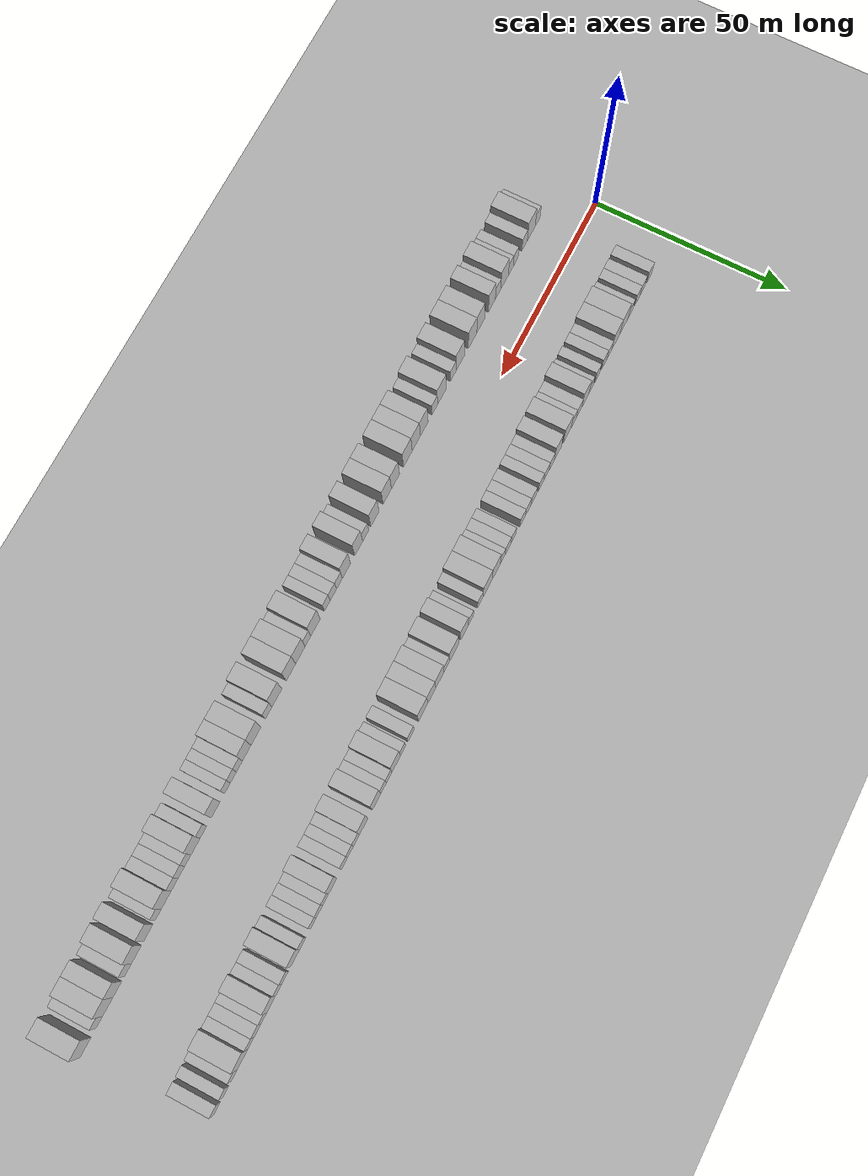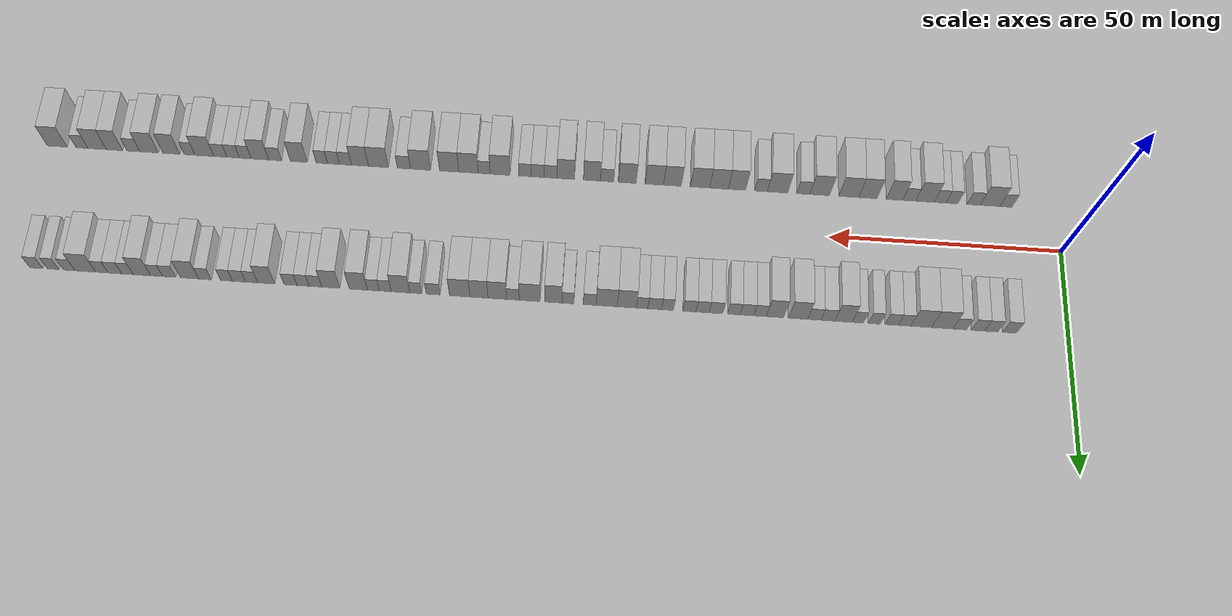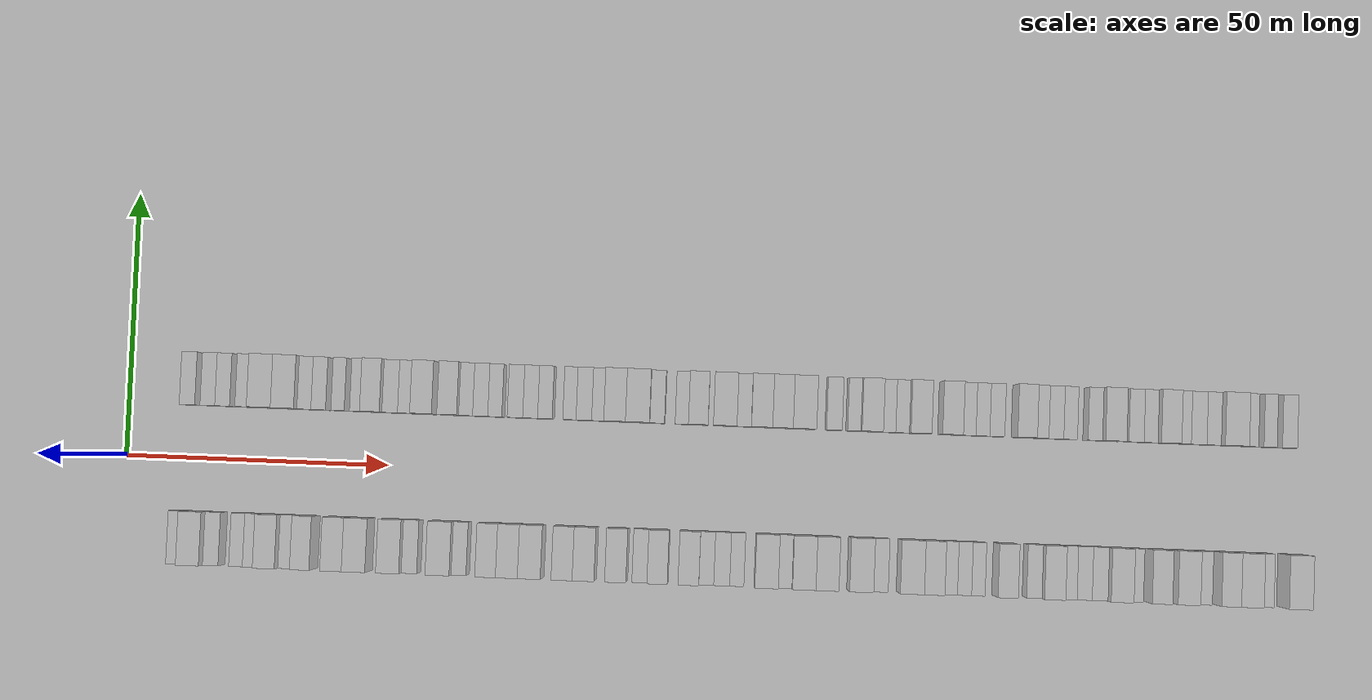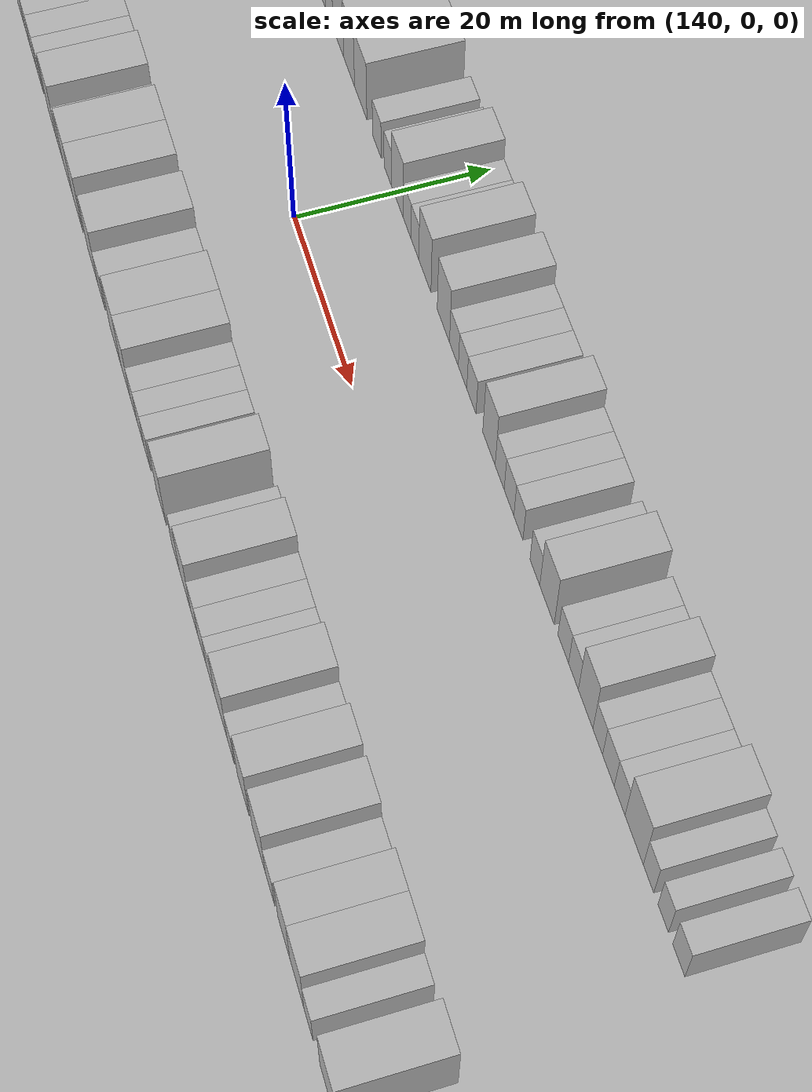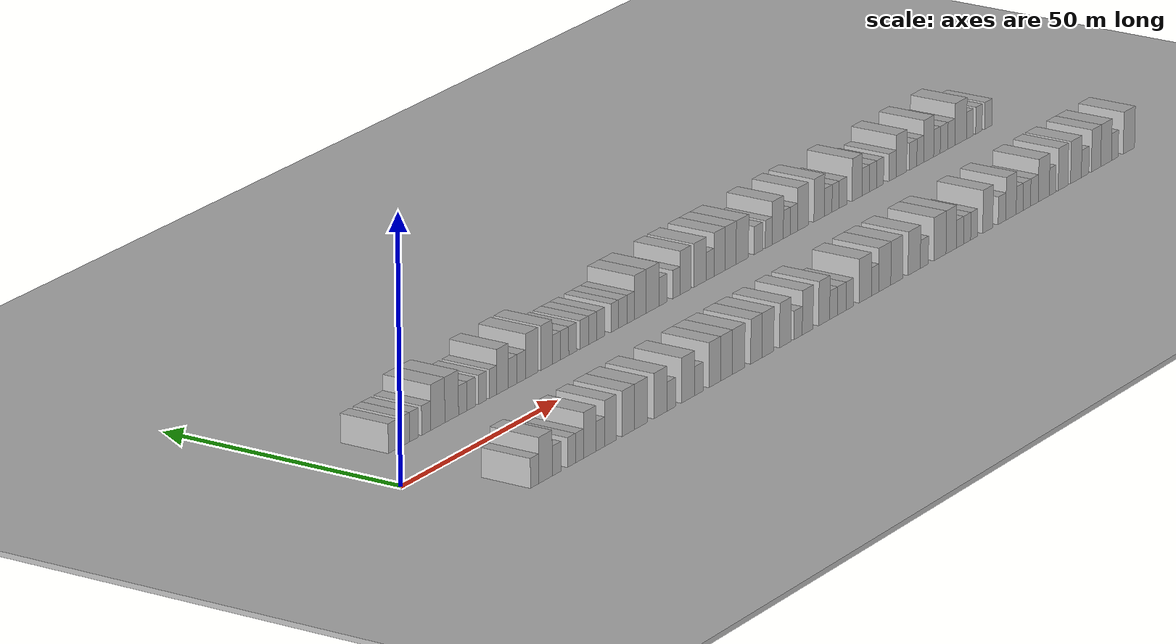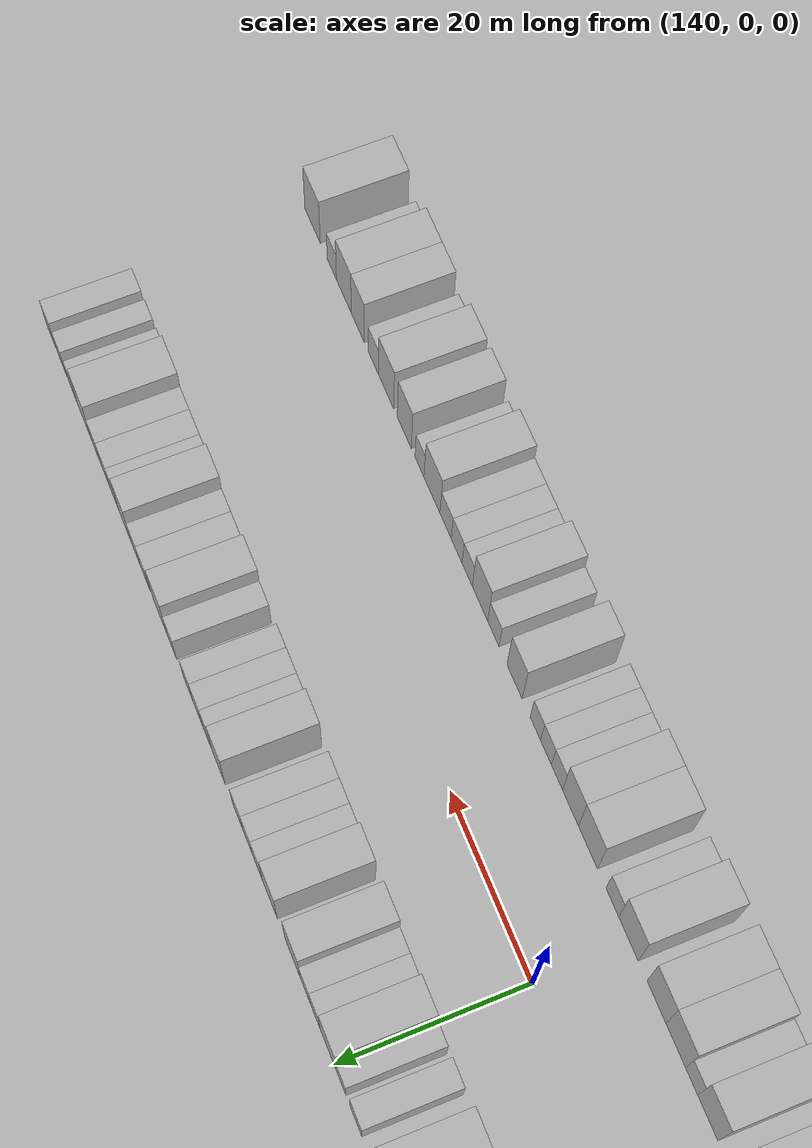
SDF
<?xml version="1.0" encoding="utf-8"?>

<sdf version="1.6">

   <world name="default">

      <gui fullscreen="0">

         <camera name="user_camera">

            <pose>-15 0 4.57585 0 0 0</pose>

            <view_controller>orbit</view_controller>

         </camera>

      </gui>

      <scene>

         <sky>

           <clouds>

             <speed>12</speed>

           </clouds>

         </sky>

         <ambient>0.4 0.4 0.4 1</ambient>

         <background>0.7 0.7 0.7 1</background>

         <shadows>1</shadows>

      </scene>

      <gravity>0 0 -9.8066</gravity>

      <magnetic_field>6e-06 2.3e-05 -4.2e-05</magnetic_field>

      <physics default="0" name="default_physics" type="ode">

         <ode>

            <solver>

               <type>quick</type>

               <iters>10</iters>

               <sor>1.0</sor>

               <use_dynamic_moi_rescaling>0</use_dynamic_moi_rescaling>

            </solver>

            <constraints>

               <cfm>0</cfm>

               <erp>0.2</erp>

               <contact_max_correcting_vel>100</contact_max_correcting_vel>

               <contact_surface_layer>0.001</contact_surface_layer>

            </constraints>

         </ode>

         <max_step_size>0.004</max_step_size>

         <real_time_factor>1</real_time_factor>

         <real_time_update_rate>250</real_time_update_rate>

      </physics>

      <light name="sun" type="directional">

         <cast_shadows>1</cast_shadows>

         <pose>0 0 10 0 0 0</pose>

         <diffuse>0.8 0.8 0.8 1</diffuse>

         <specular>0.2 0.2 0.2 1</specular>

         <attenuation>

            <range>1000</range>

            <constant>0.9</constant>

            <linear>0.01</linear>

            <quadratic>0.001</quadratic>

         </attenuation>

         <direction>-0.5 0.1 -0.9</direction>

      </light>

      <include>

         <name>ground_plane_1</name>

         <uri>model://HANNAS_ground_plane</uri>

         <pose>0 0 0  0 0 0</pose>

      </include>

      <include>

         <name>ground_plane_2</name>

         <uri>model://HANNAS_ground_plane</uri>

         <pose>100 0 0  0 0 0</pose>

      </include>

      <model name="building_1">

         <static>1</static>

         <pose frame="">12.4577 15.0000 0 0.000000 0.000000 1.570796</pose>

         <link name="link">

            <pose frame="">0 0 3.00 0 0 0</pose>

            <collision name="collision">

               <geometry>

                  <box>

                     <size>10.0000 2.9153 6.0000</size>

                  </box>

               </geometry>

               <max_contacts>10</max_contacts>

               <surface>

                  <contact>

                     <ode/>

                  </contact>

                  <bounce/>

                  <friction>

                     <torsional>

                        <ode/>

                     </torsional>

                     <ode/>

                  </friction>

               </surface>

            </collision>

            <visual name="visual">

               <cast_shadows>0</cast_shadows>

               <geometry>

                  <box>

                     <size>10.0000 2.9153 6.0000</size>

                  </box>

               </geometry>

               <material>

                  <script>

                     <uri>model://HANNAS_wall/materials/scripts</uri>

                     <uri>model://HANNAS_wall/materials/textures</uri>

                     <name>vrc/HANNAS_wall</name>

                  </script>

               </material>

            </visual>

            <self_collide>0</self_collide>

            <enable_wind>0</enable_wind>

            <kinematic>0</kinematic>

         </link>

      </model>

      <model name="building_2">

         <static>1</static>

         <pose frame="">16.3046 15.0000 0 0.000000 0.000000 1.570796</pose>

         <link name="link">

            <pose frame="">0 0 3.00 0 0 0</pose>

            <collision name="collision">

               <geometry>

                  <box>

                     <size>10.0000 2.7787 6.0000</size>

                  </box>

               </geometry>

               <max_contacts>10</max_contacts>

               <surface>

                  <contact>

                     <ode/>

                  </contact>

                  <bounce/>

                  <friction>

                     <torsional>

                        <ode/>

                     </torsional>

                     <ode/>

                  </friction>

               </surface>

            </collision>

            <visual name="visual">

               <cast_shadows>0</cast_shadows>

               <geometry>

                  <box>

                     <size>10.0000 2.7787 6.0000</size>

                  </box>

               </geometry>

               <material>

                  <script>

                     <uri>model://HANNAS_wall/materials/scripts</uri>

                     <uri>model://HANNAS_wall/materials/textures</uri>

                     <name>vrc/HANNAS_wall</name>

                  </script>

               </material>

            </visual>

            <self_collide>0</self_collide>

            <enable_wind>0</enable_wind>

            <kinematic>0</kinematic>

         </link>

      </model>

      <model name="building_3">

         <static>1</static>

         <pose frame="">19.0882 15.0000 0 0.000000 0.000000 1.570796</pose>

         <link name="link">

            <pose frame="">0 0 3.00 0 0 0</pose>

            <collision name="collision">

               <geometry>

                  <box>

                     <size>10.0000 2.7884 6.0000</size>

                  </box>

               </geometry>

               <max_contacts>10</max_contacts>

               <surface>

                  <contact>

                     <ode/>

                  </contact>

                  <bounce/>

                  <friction>

                     <torsional>

                        <ode/>

                     </torsional>

                     <ode/>

                  </friction>

               </surface>

            </collision>

            <visual name="visual">

               <cast_shadows>0</cast_shadows>

               <geometry>

                  <box>

                     <size>10.0000 2.7884 6.0000</size>

                  </box>

               </geometry>

               <material>

                  <script>

                     <uri>model://HANNAS_wall/materials/scripts</uri>

                     <uri>model://HANNAS_wall/materials/textures</uri>

                     <name>vrc/HANNAS_wall</name>

                  </script>

               </material>

            </visual>

            <self_collide>0</self_collide>

            <enable_wind>0</enable_wind>

            <kinematic>0</kinematic>

         </link>

      </model>

      <model name="building_4">

         <static>1</static>

         <pose frame="">22.9180 15.0000 0 0.000000 0.000000 1.570796</pose>

         <link name="link">

            <pose frame="">0 0 3.00 0 0 0</pose>

            <collision name="collision">

               <geometry>

                  <box>

                     <size>10.0000 2.8712 6.0000</size>

                  </box>

               </geometry>

               <max_contacts>10</max_contacts>

               <surface>

                  <contact>

                     <ode/>

                  </contact>

                  <bounce/>

                  <friction>

                     <torsional>

                        <ode/>

                     </torsional>

                     <ode/>

                  </friction>

               </surface>

            </collision>

            <visual name="visual">

               <cast_shadows>0</cast_shadows>

               <geometry>

                  <box>

                     <size>10.0000 2.8712 6.0000</size>

                  </box>

               </geometry>

               <material>

                  <script>

                     <uri>model://HANNAS_wall/materials/scripts</uri>

                     <uri>model://HANNAS_wall/materials/textures</uri>

                     <name>vrc/HANNAS_wall</name>

                  </script>

               </material>

            </visual>

            <self_collide>0</self_collide>

            <enable_wind>0</enable_wind>

            <kinematic>0</kinematic>

         </link>

      </model>

      <model name="building_5">

         <static>1</static>

         <pose frame="">26.5906 15.0000 0 0.000000 0.000000 1.570796</pose>

         <link name="link">

            <pose frame="">0 0 4.50 0 0 0</pose>

            <collision name="collision">

               <geometry>

                  <box>

                     <size>10.0000 4.4740 9.0000</size>

                  </box>

               </geometry>

               <max_contacts>10</max_contacts>

               <surface>

                  <contact>

                     <ode/>

                  </contact>

                  <bounce/>

                  <friction>

                     <torsional>

                        <ode/>

                     </torsional>

                     <ode/>

                  </friction>

               </surface>

            </collision>

            <visual name="visual">

               <cast_shadows>0</cast_shadows>

               <geometry>

                  <box>

                     <size>10.0000 4.4740 9.0000</size>

                  </box>

               </geometry>

               <material>

                  <script>

                     <uri>model://HANNAS_wall/materials/scripts</uri>

                     <uri>model://HANNAS_wall/materials/textures</uri>

                     <name>vrc/HANNAS_wall</name>

                  </script>

               </material>

            </visual>

            <self_collide>0</self_collide>

            <enable_wind>0</enable_wind>

            <kinematic>0</kinematic>

         </link>

      </model>

      <model name="building_6">

         <static>1</static>

         <pose frame="">31.0061 15.0000 0 0.000000 0.000000 1.570796</pose>

         <link name="link">

            <pose frame="">0 0 4.50 0 0 0</pose>

            <collision name="collision">

               <geometry>

                  <box>

                     <size>10.0000 4.3570 9.0000</size>

                  </box>

               </geometry>

               <max_contacts>10</max_contacts>

               <surface>

                  <contact>

                     <ode/>

                  </contact>

                  <bounce/>

                  <friction>

                     <torsional>

                        <ode/>

                     </torsional>

                     <ode/>

                  </friction>

               </surface>

            </collision>

            <visual name="visual">

               <cast_shadows>0</cast_shadows>

               <geometry>

                  <box>

                     <size>10.0000 4.3570 9.0000</size>

                  </box>

               </geometry>

               <material>

                  <script>

                     <uri>model://HANNAS_wall/materials/scripts</uri>

                     <uri>model://HANNAS_wall/materials/textures</uri>

                     <name>vrc/HANNAS_wall</name>

                  </script>

               </material>

            </visual>

            <self_collide>0</self_collide>

            <enable_wind>0</enable_wind>

            <kinematic>0</kinematic>

         </link>

      </model>

      <model name="building_7">

         <static>1</static>

         <pose frame="">34.4990 15.0000 0 0.000000 0.000000 1.570796</pose>

         <link name="link">

            <pose frame="">0 0 3.00 0 0 0</pose>

            <collision name="collision">

               <geometry>

                  <box>

                     <size>10.0000 2.6288 6.0000</size>

                  </box>

               </geometry>

               <max_contacts>10</max_contacts>

               <surface>

                  <contact>

                     <ode/>

                  </contact>

                  <bounce/>

                  <friction>

                     <torsional>

                        <ode/>

                     </torsional>

                     <ode/>

                  </friction>

               </surface>

            </collision>

            <visual name="visual">

               <cast_shadows>0</cast_shadows>

               <geometry>

                  <box>

                     <size>10.0000 2.6288 6.0000</size>

                  </box>

               </geometry>

               <material>

                  <script>

                     <uri>model://HANNAS_wall/materials/scripts</uri>

                     <uri>model://HANNAS_wall/materials/textures</uri>

                     <name>vrc/HANNAS_wall</name>

                  </script>

               </material>

            </visual>

            <self_collide>0</self_collide>

            <enable_wind>0</enable_wind>

            <kinematic>0</kinematic>

         </link>

      </model>

      <model name="building_8">

         <static>1</static>

         <pose frame="">37.1985 15.0000 0 0.000000 0.000000 1.570796</pose>

         <link name="link">

            <pose frame="">0 0 3.00 0 0 0</pose>

            <collision name="collision">

               <geometry>

                  <box>

                     <size>10.0000 2.7701 6.0000</size>

                  </box>

               </geometry>

               <max_contacts>10</max_contacts>

               <surface>

                  <contact>

                     <ode/>

                  </contact>

                  <bounce/>

                  <friction>

                     <torsional>

                        <ode/>

                     </torsional>

                     <ode/>

                  </friction>

               </surface>

            </collision>

            <visual name="visual">

               <cast_shadows>0</cast_shadows>

               <geometry>

                  <box>

                     <size>10.0000 2.7701 6.0000</size>

                  </box>

               </geometry>

               <material>

                  <script>

                     <uri>model://HANNAS_wall/materials/scripts</uri>

                     <uri>model://HANNAS_wall/materials/textures</uri>

                     <name>vrc/HANNAS_wall</name>

                  </script>

               </material>

            </visual>

            <self_collide>0</self_collide>

            <enable_wind>0</enable_wind>

            <kinematic>0</kinematic>

         </link>

      </model>

      <model name="building_9">

         <static>1</static>

         <pose frame="">40.8424 15.0000 0 0.000000 0.000000 1.570796</pose>

         <link name="link">

            <pose frame="">0 0 3.00 0 0 0</pose>

            <collision name="collision">

               <geometry>

                  <box>

                     <size>10.0000 2.5178 6.0000</size>

                  </box>

               </geometry>

               <max_contacts>10</max_contacts>

               <surface>

                  <contact>

                     <ode/>

                  </contact>

                  <bounce/>

                  <friction>

                     <torsional>

                        <ode/>

                     </torsional>

                     <ode/>

                  </friction>

               </surface>

            </collision>

            <visual name="visual">

               <cast_shadows>0</cast_shadows>

               <geometry>

                  <box>

                     <size>10.0000 2.5178 6.0000</size>

                  </box>

               </geometry>

               <material>

                  <script>

                     <uri>model://HANNAS_wall/materials/scripts</uri>

                     <uri>model://HANNAS_wall/materials/textures</uri>

                     <name>vrc/HANNAS_wall</name>

                  </script>

               </material>

            </visual>

            <self_collide>0</self_collide>

            <enable_wind>0</enable_wind>

            <kinematic>0</kinematic>

         </link>

      </model>

      <model name="building_10">

         <static>1</static>

         <pose frame="">44.3051 15.0000 0 0.000000 0.000000 1.570796</pose>

         <link name="link">

            <pose frame="">0 0 3.00 0 0 0</pose>

            <collision name="collision">

               <geometry>

                  <box>

                     <size>10.0000 2.4076 6.0000</size>

                  </box>

               </geometry>

               <max_contacts>10</max_contacts>

               <surface>

                  <contact>

                     <ode/>

                  </contact>

                  <bounce/>

                  <friction>

                     <torsional>

                        <ode/>

                     </torsional>

                     <ode/>

                  </friction>

               </surface>

            </collision>

            <visual name="visual">

               <cast_shadows>0</cast_shadows>

               <geometry>

                  <box>

                     <size>10.0000 2.4076 6.0000</size>

                  </box>

               </geometry>

               <material>

                  <script>

                     <uri>model://HANNAS_wall/materials/scripts</uri>

                     <uri>model://HANNAS_wall/materials/textures</uri>

                     <name>vrc/HANNAS_wall</name>

                  </script>

               </material>

            </visual>

            <self_collide>0</self_collide>

            <enable_wind>0</enable_wind>

            <kinematic>0</kinematic>

         </link>

      </model>

      <model name="building_11">

         <static>1</static>

         <pose frame="">47.3543 15.0000 0 0.000000 0.000000 1.570796</pose>

         <link name="link">

            <pose frame="">0 0 4.50 0 0 0</pose>

            <collision name="collision">

               <geometry>

                  <box>

                     <size>10.0000 3.6907 9.0000</size>

                  </box>

               </geometry>

               <max_contacts>10</max_contacts>

               <surface>

                  <contact>

                     <ode/>

                  </contact>

                  <bounce/>

                  <friction>

                     <torsional>

                        <ode/>

                     </torsional>

                     <ode/>

                  </friction>

               </surface>

            </collision>

            <visual name="visual">

               <cast_shadows>0</cast_shadows>

               <geometry>

                  <box>

                     <size>10.0000 3.6907 9.0000</size>

                  </box>

               </geometry>

               <material>

                  <script>

                     <uri>model://HANNAS_wall/materials/scripts</uri>

                     <uri>model://HANNAS_wall/materials/textures</uri>

                     <name>vrc/HANNAS_wall</name>

                  </script>

               </material>

            </visual>

            <self_collide>0</self_collide>

            <enable_wind>0</enable_wind>

            <kinematic>0</kinematic>

         </link>

      </model>

      <model name="building_12">

         <static>1</static>

         <pose frame="">50.6692 15.0000 0 0.000000 0.000000 1.570796</pose>

         <link name="link">

            <pose frame="">0 0 3.00 0 0 0</pose>

            <collision name="collision">

               <geometry>

                  <box>

                     <size>10.0000 2.9390 6.0000</size>

                  </box>

               </geometry>

               <max_contacts>10</max_contacts>

               <surface>

                  <contact>

                     <ode/>

                  </contact>

                  <bounce/>

                  <friction>

                     <torsional>

                        <ode/>

                     </torsional>

                     <ode/>

                  </friction>

               </surface>

            </collision>

            <visual name="visual">

               <cast_shadows>0</cast_shadows>

               <geometry>

                  <box>

                     <size>10.0000 2.9390 6.0000</size>

                  </box>

               </geometry>

               <material>

                  <script>

                     <uri>model://HANNAS_wall/materials/scripts</uri>

                     <uri>model://HANNAS_wall/materials/textures</uri>

                     <name>vrc/HANNAS_wall</name>

                  </script>

               </material>

            </visual>

            <self_collide>0</self_collide>

            <enable_wind>0</enable_wind>

            <kinematic>0</kinematic>

         </link>

      </model>

      <model name="building_13">

         <static>1</static>

         <pose frame="">53.5088 15.0000 0 0.000000 0.000000 1.570796</pose>

         <link name="link">

            <pose frame="">0 0 3.00 0 0 0</pose>

            <collision name="collision">

               <geometry>

                  <box>

                     <size>10.0000 2.7402 6.0000</size>

                  </box>

               </geometry>

               <max_contacts>10</max_contacts>

               <surface>

                  <contact>

                     <ode/>

                  </contact>

                  <bounce/>

                  <friction>

                     <torsional>

                        <ode/>

                     </torsional>

                     <ode/>

                  </friction>

               </surface>

            </collision>

            <visual name="visual">

               <cast_shadows>0</cast_shadows>

               <geometry>

                  <box>

                     <size>10.0000 2.7402 6.0000</size>

                  </box>

               </geometry>

               <material>

                  <script>

                     <uri>model://HANNAS_wall/materials/scripts</uri>

                     <uri>model://HANNAS_wall/materials/textures</uri>

                     <name>vrc/HANNAS_wall</name>

                  </script>

               </material>

            </visual>

            <self_collide>0</self_collide>

            <enable_wind>0</enable_wind>

            <kinematic>0</kinematic>

         </link>

      </model>

      <model name="building_14">

         <static>1</static>

         <pose frame="">56.9188 15.0000 0 0.000000 0.000000 1.570796</pose>

         <link name="link">

            <pose frame="">0 0 4.50 0 0 0</pose>

            <collision name="collision">

               <geometry>

                  <box>

                     <size>10.0000 4.0799 9.0000</size>

                  </box>

               </geometry>

               <max_contacts>10</max_contacts>

               <surface>

                  <contact>

                     <ode/>

                  </contact>

                  <bounce/>

                  <friction>

                     <torsional>

                        <ode/>

                     </torsional>

                     <ode/>

                  </friction>

               </surface>

            </collision>

            <visual name="visual">

               <cast_shadows>0</cast_shadows>

               <geometry>

                  <box>

                     <size>10.0000 4.0799 9.0000</size>

                  </box>

               </geometry>

               <material>

                  <script>

                     <uri>model://HANNAS_wall/materials/scripts</uri>

                     <uri>model://HANNAS_wall/materials/textures</uri>

                     <name>vrc/HANNAS_wall</name>

                  </script>

               </material>

            </visual>

            <self_collide>0</self_collide>

            <enable_wind>0</enable_wind>

            <kinematic>0</kinematic>

         </link>

      </model>

      <model name="building_15">

         <static>1</static>

         <pose frame="">61.8096 15.0000 0 0.000000 0.000000 1.570796</pose>

         <link name="link">

            <pose frame="">0 0 4.50 0 0 0</pose>

            <collision name="collision">

               <geometry>

                  <box>

                     <size>10.0000 3.7018 9.0000</size>

                  </box>

               </geometry>

               <max_contacts>10</max_contacts>

               <surface>

                  <contact>

                     <ode/>

                  </contact>

                  <bounce/>

                  <friction>

                     <torsional>

                        <ode/>

                     </torsional>

                     <ode/>

                  </friction>

               </surface>

            </collision>

            <visual name="visual">

               <cast_shadows>0</cast_shadows>

               <geometry>

                  <box>

                     <size>10.0000 3.7018 9.0000</size>

                  </box>

               </geometry>

               <material>

                  <script>

                     <uri>model://HANNAS_wall/materials/scripts</uri>

                     <uri>model://HANNAS_wall/materials/textures</uri>

                     <name>vrc/HANNAS_wall</name>

                  </script>

               </material>

            </visual>

            <self_collide>0</self_collide>

            <enable_wind>0</enable_wind>

            <kinematic>0</kinematic>

         </link>

      </model>

      <model name="building_16">

         <static>1</static>

         <pose frame="">64.9770 15.0000 0 0.000000 0.000000 1.570796</pose>

         <link name="link">

            <pose frame="">0 0 3.00 0 0 0</pose>

            <collision name="collision">

               <geometry>

                  <box>

                     <size>10.0000 2.6329 6.0000</size>

                  </box>

               </geometry>

               <max_contacts>10</max_contacts>

               <surface>

                  <contact>

                     <ode/>

                  </contact>

                  <bounce/>

                  <friction>

                     <torsional>

                        <ode/>

                     </torsional>

                     <ode/>

                  </friction>

               </surface>

            </collision>

            <visual name="visual">

               <cast_shadows>0</cast_shadows>

               <geometry>

                  <box>

                     <size>10.0000 2.6329 6.0000</size>

                  </box>

               </geometry>

               <material>

                  <script>

                     <uri>model://HANNAS_wall/materials/scripts</uri>

                     <uri>model://HANNAS_wall/materials/textures</uri>

                     <name>vrc/HANNAS_wall</name>

                  </script>

               </material>

            </visual>

            <self_collide>0</self_collide>

            <enable_wind>0</enable_wind>

            <kinematic>0</kinematic>

         </link>

      </model>

      <model name="building_17">

         <static>1</static>

         <pose frame="">67.7190 15.0000 0 0.000000 0.000000 1.570796</pose>

         <link name="link">

            <pose frame="">0 0 3.00 0 0 0</pose>

            <collision name="collision">

               <geometry>

                  <box>

                     <size>10.0000 2.8511 6.0000</size>

                  </box>

               </geometry>

               <max_contacts>10</max_contacts>

               <surface>

                  <contact>

                     <ode/>

                  </contact>

                  <bounce/>

                  <friction>

                     <torsional>

                        <ode/>

                     </torsional>

                     <ode/>

                  </friction>

               </surface>

            </collision>

            <visual name="visual">

               <cast_shadows>0</cast_shadows>

               <geometry>

                  <box>

                     <size>10.0000 2.8511 6.0000</size>

                  </box>

               </geometry>

               <material>

                  <script>

                     <uri>model://HANNAS_wall/materials/scripts</uri>

                     <uri>model://HANNAS_wall/materials/textures</uri>

                     <name>vrc/HANNAS_wall</name>

                  </script>

               </material>

            </visual>

            <self_collide>0</self_collide>

            <enable_wind>0</enable_wind>

            <kinematic>0</kinematic>

         </link>

      </model>

      <model name="building_18">

         <static>1</static>

         <pose frame="">70.4726 15.0000 0 0.000000 0.000000 1.570796</pose>

         <link name="link">

            <pose frame="">0 0 3.00 0 0 0</pose>

            <collision name="collision">

               <geometry>

                  <box>

                     <size>10.0000 2.6562 6.0000</size>

                  </box>

               </geometry>

               <max_contacts>10</max_contacts>

               <surface>

                  <contact>

                     <ode/>

                  </contact>

                  <bounce/>

                  <friction>

                     <torsional>

                        <ode/>

                     </torsional>

                     <ode/>

                  </friction>

               </surface>

            </collision>

            <visual name="visual">

               <cast_shadows>0</cast_shadows>

               <geometry>

                  <box>

                     <size>10.0000 2.6562 6.0000</size>

                  </box>

               </geometry>

               <material>

                  <script>

                     <uri>model://HANNAS_wall/materials/scripts</uri>

                     <uri>model://HANNAS_wall/materials/textures</uri>

                     <name>vrc/HANNAS_wall</name>

                  </script>

               </material>

            </visual>

            <self_collide>0</self_collide>

            <enable_wind>0</enable_wind>

            <kinematic>0</kinematic>

         </link>

      </model>

      <model name="building_19">

         <static>1</static>

         <pose frame="">74.2659 15.0000 0 0.000000 0.000000 1.570796</pose>

         <link name="link">

            <pose frame="">0 0 3.00 0 0 0</pose>

            <collision name="collision">

               <geometry>

                  <box>

                     <size>10.0000 2.9304 6.0000</size>

                  </box>

               </geometry>

               <max_contacts>10</max_contacts>

               <surface>

                  <contact>

                     <ode/>

                  </contact>

                  <bounce/>

                  <friction>

                     <torsional>

                        <ode/>

                     </torsional>

                     <ode/>

                  </friction>

               </surface>

            </collision>

            <visual name="visual">

               <cast_shadows>0</cast_shadows>

               <geometry>

                  <box>

                     <size>10.0000 2.9304 6.0000</size>

                  </box>

               </geometry>

               <material>

                  <script>

                     <uri>model://HANNAS_wall/materials/scripts</uri>

                     <uri>model://HANNAS_wall/materials/textures</uri>

                     <name>vrc/HANNAS_wall</name>

                  </script>

               </material>

            </visual>

            <self_collide>0</self_collide>

            <enable_wind>0</enable_wind>

            <kinematic>0</kinematic>

         </link>

      </model>

      <model name="building_20">

         <static>1</static>

         <pose frame="">77.1341 15.0000 0 0.000000 0.000000 1.570796</pose>

         <link name="link">

            <pose frame="">0 0 3.00 0 0 0</pose>

            <collision name="collision">

               <geometry>

                  <box>

                     <size>10.0000 2.8060 6.0000</size>

                  </box>

               </geometry>

               <max_contacts>10</max_contacts>

               <surface>

                  <contact>

                     <ode/>

                  </contact>

                  <bounce/>

                  <friction>

                     <torsional>

                        <ode/>

                     </torsional>

                     <ode/>

                  </friction>

               </surface>

            </collision>

            <visual name="visual">

               <cast_shadows>0</cast_shadows>

               <geometry>

                  <box>

                     <size>10.0000 2.8060 6.0000</size>

                  </box>

               </geometry>

               <material>

                  <script>

                     <uri>model://HANNAS_wall/materials/scripts</uri>

                     <uri>model://HANNAS_wall/materials/textures</uri>

                     <name>vrc/HANNAS_wall</name>

                  </script>

               </material>

            </visual>

            <self_collide>0</self_collide>

            <enable_wind>0</enable_wind>

            <kinematic>0</kinematic>

         </link>

      </model>

      <model name="building_21">

         <static>1</static>

         <pose frame="">79.9107 15.0000 0 0.000000 0.000000 1.570796</pose>

         <link name="link">

            <pose frame="">0 0 3.00 0 0 0</pose>

            <collision name="collision">

               <geometry>

                  <box>

                     <size>10.0000 2.7471 6.0000</size>

                  </box>

               </geometry>

               <max_contacts>10</max_contacts>

               <surface>

                  <contact>

                     <ode/>

                  </contact>

                  <bounce/>

                  <friction>

                     <torsional>

                        <ode/>

                     </torsional>

                     <ode/>

                  </friction>

               </surface>

            </collision>

            <visual name="visual">

               <cast_shadows>0</cast_shadows>

               <geometry>

                  <box>

                     <size>10.0000 2.7471 6.0000</size>

                  </box>

               </geometry>

               <material>

                  <script>

                     <uri>model://HANNAS_wall/materials/scripts</uri>

                     <uri>model://HANNAS_wall/materials/textures</uri>

                     <name>vrc/HANNAS_wall</name>

                  </script>

               </material>

            </visual>

            <self_collide>0</self_collide>

            <enable_wind>0</enable_wind>

            <kinematic>0</kinematic>

         </link>

      </model>

      <model name="building_22">

         <static>1</static>

         <pose frame="">84.5346 15.0000 0 0.000000 0.000000 1.570796</pose>

         <link name="link">

            <pose frame="">0 0 3.00 0 0 0</pose>

            <collision name="collision">

               <geometry>

                  <box>

                     <size>10.0000 2.5008 6.0000</size>

                  </box>

               </geometry>

               <max_contacts>10</max_contacts>

               <surface>

                  <contact>

                     <ode/>

                  </contact>

                  <bounce/>

                  <friction>

                     <torsional>

                        <ode/>

                     </torsional>

                     <ode/>

                  </friction>

               </surface>

            </collision>

            <visual name="visual">

               <cast_shadows>0</cast_shadows>

               <geometry>

                  <box>

                     <size>10.0000 2.5008 6.0000</size>

                  </box>

               </geometry>

               <material>

                  <script>

                     <uri>model://HANNAS_wall/materials/scripts</uri>

                     <uri>model://HANNAS_wall/materials/textures</uri>

                     <name>vrc/HANNAS_wall</name>

                  </script>

               </material>

            </visual>

            <self_collide>0</self_collide>

            <enable_wind>0</enable_wind>

            <kinematic>0</kinematic>

         </link>

      </model>

      <model name="building_23">

         <static>1</static>

         <pose frame="">87.2518 15.0000 0 0.000000 0.000000 1.570796</pose>

         <link name="link">

            <pose frame="">0 0 3.00 0 0 0</pose>

            <collision name="collision">

               <geometry>

                  <box>

                     <size>10.0000 2.9336 6.0000</size>

                  </box>

               </geometry>

               <max_contacts>10</max_contacts>

               <surface>

                  <contact>

                     <ode/>

                  </contact>

                  <bounce/>

                  <friction>

                     <torsional>

                        <ode/>

                     </torsional>

                     <ode/>

                  </friction>

               </surface>

            </collision>

            <visual name="visual">

               <cast_shadows>0</cast_shadows>

               <geometry>

                  <box>

                     <size>10.0000 2.9336 6.0000</size>

                  </box>

               </geometry>

               <material>

                  <script>

                     <uri>model://HANNAS_wall/materials/scripts</uri>

                     <uri>model://HANNAS_wall/materials/textures</uri>

                     <name>vrc/HANNAS_wall</name>

                  </script>

               </material>

            </visual>

            <self_collide>0</self_collide>

            <enable_wind>0</enable_wind>

            <kinematic>0</kinematic>

         </link>

      </model>

      <model name="building_24">

         <static>1</static>

         <pose frame="">89.9448 15.0000 0 0.000000 0.000000 1.570796</pose>

         <link name="link">

            <pose frame="">0 0 3.00 0 0 0</pose>

            <collision name="collision">

               <geometry>

                  <box>

                     <size>10.0000 2.4523 6.0000</size>

                  </box>

               </geometry>

               <max_contacts>10</max_contacts>

               <surface>

                  <contact>

                     <ode/>

                  </contact>

                  <bounce/>

                  <friction>

                     <torsional>

                        <ode/>

                     </torsional>

                     <ode/>

                  </friction>

               </surface>

            </collision>

            <visual name="visual">

               <cast_shadows>0</cast_shadows>

               <geometry>

                  <box>

                     <size>10.0000 2.4523 6.0000</size>

                  </box>

               </geometry>

               <material>

                  <script>

                     <uri>model://HANNAS_wall/materials/scripts</uri>

                     <uri>model://HANNAS_wall/materials/textures</uri>

                     <name>vrc/HANNAS_wall</name>

                  </script>

               </material>

            </visual>

            <self_collide>0</self_collide>

            <enable_wind>0</enable_wind>

            <kinematic>0</kinematic>

         </link>

      </model>

      <model name="building_25">

         <static>1</static>

         <pose frame="">93.1977 15.0000 0 0.000000 0.000000 1.570796</pose>

         <link name="link">

            <pose frame="">0 0 4.50 0 0 0</pose>

            <collision name="collision">

               <geometry>

                  <box>

                     <size>10.0000 4.0536 9.0000</size>

                  </box>

               </geometry>

               <max_contacts>10</max_contacts>

               <surface>

                  <contact>

                     <ode/>

                  </contact>

                  <bounce/>

                  <friction>

                     <torsional>

                        <ode/>

                     </torsional>

                     <ode/>

                  </friction>

               </surface>

            </collision>

            <visual name="visual">

               <cast_shadows>0</cast_shadows>

               <geometry>

                  <box>

                     <size>10.0000 4.0536 9.0000</size>

                  </box>

               </geometry>

               <material>

                  <script>

                     <uri>model://HANNAS_wall/materials/scripts</uri>

                     <uri>model://HANNAS_wall/materials/textures</uri>

                     <name>vrc/HANNAS_wall</name>

                  </script>

               </material>

            </visual>

            <self_collide>0</self_collide>

            <enable_wind>0</enable_wind>

            <kinematic>0</kinematic>

         </link>

      </model>

      <model name="building_26">

         <static>1</static>

         <pose frame="">97.4699 15.0000 0 0.000000 0.000000 1.570796</pose>

         <link name="link">

            <pose frame="">0 0 4.50 0 0 0</pose>

            <collision name="collision">

               <geometry>

                  <box>

                     <size>10.0000 4.4908 9.0000</size>

                  </box>

               </geometry>

               <max_contacts>10</max_contacts>

               <surface>

                  <contact>

                     <ode/>

                  </contact>

                  <bounce/>

                  <friction>

                     <torsional>

                        <ode/>

                     </torsional>

                     <ode/>

                  </friction>

               </surface>

            </collision>

            <visual name="visual">

               <cast_shadows>0</cast_shadows>

               <geometry>

                  <box>

                     <size>10.0000 4.4908 9.0000</size>

                  </box>

               </geometry>

               <material>

                  <script>

                     <uri>model://HANNAS_wall/materials/scripts</uri>

                     <uri>model://HANNAS_wall/materials/textures</uri>

                     <name>vrc/HANNAS_wall</name>

                  </script>

               </material>

            </visual>

            <self_collide>0</self_collide>

            <enable_wind>0</enable_wind>

            <kinematic>0</kinematic>

         </link>

      </model>

      <model name="building_27">

         <static>1</static>

         <pose frame="">101.0842 15.0000 0 0.000000 0.000000 1.570796</pose>

         <link name="link">

            <pose frame="">0 0 3.00 0 0 0</pose>

            <collision name="collision">

               <geometry>

                  <box>

                     <size>10.0000 2.7377 6.0000</size>

                  </box>

               </geometry>

               <max_contacts>10</max_contacts>

               <surface>

                  <contact>

                     <ode/>

                  </contact>

                  <bounce/>

                  <friction>

                     <torsional>

                        <ode/>

                     </torsional>

                     <ode/>

                  </friction>

               </surface>

            </collision>

            <visual name="visual">

               <cast_shadows>0</cast_shadows>

               <geometry>

                  <box>

                     <size>10.0000 2.7377 6.0000</size>

                  </box>

               </geometry>

               <material>

                  <script>

                     <uri>model://HANNAS_wall/materials/scripts</uri>

                     <uri>model://HANNAS_wall/materials/textures</uri>

                     <name>vrc/HANNAS_wall</name>

                  </script>

               </material>

            </visual>

            <self_collide>0</self_collide>

            <enable_wind>0</enable_wind>

            <kinematic>0</kinematic>

         </link>

      </model>

      <model name="building_28">

         <static>1</static>

         <pose frame="">105.7235 15.0000 0 0.000000 0.000000 1.570796</pose>

         <link name="link">

            <pose frame="">0 0 3.00 0 0 0</pose>

            <collision name="collision">

               <geometry>

                  <box>

                     <size>10.0000 2.5409 6.0000</size>

                  </box>

               </geometry>

               <max_contacts>10</max_contacts>

               <surface>

                  <contact>

                     <ode/>

                  </contact>

                  <bounce/>

                  <friction>

                     <torsional>

                        <ode/>

                     </torsional>

                     <ode/>

                  </friction>

               </surface>

            </collision>

            <visual name="visual">

               <cast_shadows>0</cast_shadows>

               <geometry>

                  <box>

                     <size>10.0000 2.5409 6.0000</size>

                  </box>

               </geometry>

               <material>

                  <script>

                     <uri>model://HANNAS_wall/materials/scripts</uri>

                     <uri>model://HANNAS_wall/materials/textures</uri>

                     <name>vrc/HANNAS_wall</name>

                  </script>

               </material>

            </visual>

            <self_collide>0</self_collide>

            <enable_wind>0</enable_wind>

            <kinematic>0</kinematic>

         </link>

      </model>

      <model name="building_29">

         <static>1</static>

         <pose frame="">108.8355 15.0000 0 0.000000 0.000000 1.570796</pose>

         <link name="link">

            <pose frame="">0 0 4.50 0 0 0</pose>

            <collision name="collision">

               <geometry>

                  <box>

                     <size>10.0000 3.6832 9.0000</size>

                  </box>

               </geometry>

               <max_contacts>10</max_contacts>

               <surface>

                  <contact>

                     <ode/>

                  </contact>

                  <bounce/>

                  <friction>

                     <torsional>

                        <ode/>

                     </torsional>

                     <ode/>

                  </friction>

               </surface>

            </collision>

            <visual name="visual">

               <cast_shadows>0</cast_shadows>

               <geometry>

                  <box>

                     <size>10.0000 3.6832 9.0000</size>

                  </box>

               </geometry>

               <material>

                  <script>

                     <uri>model://HANNAS_wall/materials/scripts</uri>

                     <uri>model://HANNAS_wall/materials/textures</uri>

                     <name>vrc/HANNAS_wall</name>

                  </script>

               </material>

            </visual>

            <self_collide>0</self_collide>

            <enable_wind>0</enable_wind>

            <kinematic>0</kinematic>

         </link>

      </model>

      <model name="building_30">

         <static>1</static>

         <pose frame="">113.8813 15.0000 0 0.000000 0.000000 1.570796</pose>

         <link name="link">

            <pose frame="">0 0 4.50 0 0 0</pose>

            <collision name="collision">

               <geometry>

                  <box>

                     <size>10.0000 4.4084 9.0000</size>

                  </box>

               </geometry>

               <max_contacts>10</max_contacts>

               <surface>

                  <contact>

                     <ode/>

                  </contact>

                  <bounce/>

                  <friction>

                     <torsional>

                        <ode/>

                     </torsional>

                     <ode/>

                  </friction>

               </surface>

            </collision>

            <visual name="visual">

               <cast_shadows>0</cast_shadows>

               <geometry>

                  <box>

                     <size>10.0000 4.4084 9.0000</size>

                  </box>

               </geometry>

               <material>

                  <script>

                     <uri>model://HANNAS_wall/materials/scripts</uri>

                     <uri>model://HANNAS_wall/materials/textures</uri>

                     <name>vrc/HANNAS_wall</name>

                  </script>

               </material>

            </visual>

            <self_collide>0</self_collide>

            <enable_wind>0</enable_wind>

            <kinematic>0</kinematic>

         </link>

      </model>

      <model name="building_31">

         <static>1</static>

         <pose frame="">117.4507 15.0000 0 0.000000 0.000000 1.570796</pose>

         <link name="link">

            <pose frame="">0 0 3.00 0 0 0</pose>

            <collision name="collision">

               <geometry>

                  <box>

                     <size>10.0000 2.7305 6.0000</size>

                  </box>

               </geometry>

               <max_contacts>10</max_contacts>

               <surface>

                  <contact>

                     <ode/>

                  </contact>

                  <bounce/>

                  <friction>

                     <torsional>

                        <ode/>

                     </torsional>

                     <ode/>

                  </friction>

               </surface>

            </collision>

            <visual name="visual">

               <cast_shadows>0</cast_shadows>

               <geometry>

                  <box>

                     <size>10.0000 2.7305 6.0000</size>

                  </box>

               </geometry>

               <material>

                  <script>

                     <uri>model://HANNAS_wall/materials/scripts</uri>

                     <uri>model://HANNAS_wall/materials/textures</uri>

                     <name>vrc/HANNAS_wall</name>

                  </script>

               </material>

            </visual>

            <self_collide>0</self_collide>

            <enable_wind>0</enable_wind>

            <kinematic>0</kinematic>

         </link>

      </model>

      <model name="building_32">

         <static>1</static>

         <pose frame="">120.7867 15.0000 0 0.000000 0.000000 1.570796</pose>

         <link name="link">

            <pose frame="">0 0 4.50 0 0 0</pose>

            <collision name="collision">

               <geometry>

                  <box>

                     <size>10.0000 3.9415 9.0000</size>

                  </box>

               </geometry>

               <max_contacts>10</max_contacts>

               <surface>

                  <contact>

                     <ode/>

                  </contact>

                  <bounce/>

                  <friction>

                     <torsional>

                        <ode/>

                     </torsional>

                     <ode/>

                  </friction>

               </surface>

            </collision>

            <visual name="visual">

               <cast_shadows>0</cast_shadows>

               <geometry>

                  <box>

                     <size>10.0000 3.9415 9.0000</size>

                  </box>

               </geometry>

               <material>

                  <script>

                     <uri>model://HANNAS_wall/materials/scripts</uri>

                     <uri>model://HANNAS_wall/materials/textures</uri>

                     <name>vrc/HANNAS_wall</name>

                  </script>

               </material>

            </visual>

            <self_collide>0</self_collide>

            <enable_wind>0</enable_wind>

            <kinematic>0</kinematic>

         </link>

      </model>

      <model name="building_33">

         <static>1</static>

         <pose frame="">124.6819 15.0000 0 0.000000 0.000000 1.570796</pose>

         <link name="link">

            <pose frame="">0 0 4.50 0 0 0</pose>

            <collision name="collision">

               <geometry>

                  <box>

                     <size>10.0000 3.8489 9.0000</size>

                  </box>

               </geometry>

               <max_contacts>10</max_contacts>

               <surface>

                  <contact>

                     <ode/>

                  </contact>

                  <bounce/>

                  <friction>

                     <torsional>

                        <ode/>

                     </torsional>

                     <ode/>

                  </friction>

               </surface>

            </collision>

            <visual name="visual">

               <cast_shadows>0</cast_shadows>

               <geometry>

                  <box>

                     <size>10.0000 3.8489 9.0000</size>

                  </box>

               </geometry>

               <material>

                  <script>

                     <uri>model://HANNAS_wall/materials/scripts</uri>

                     <uri>model://HANNAS_wall/materials/textures</uri>

                     <name>vrc/HANNAS_wall</name>

                  </script>

               </material>

            </visual>

            <self_collide>0</self_collide>

            <enable_wind>0</enable_wind>

            <kinematic>0</kinematic>

         </link>

      </model>

      <model name="building_34">

         <static>1</static>

         <pose frame="">128.7969 15.0000 0 0.000000 0.000000 1.570796</pose>

         <link name="link">

            <pose frame="">0 0 4.50 0 0 0</pose>

            <collision name="collision">

               <geometry>

                  <box>

                     <size>10.0000 4.3810 9.0000</size>

                  </box>

               </geometry>

               <max_contacts>10</max_contacts>

               <surface>

                  <contact>

                     <ode/>

                  </contact>

                  <bounce/>

                  <friction>

                     <torsional>

                        <ode/>

                     </torsional>

                     <ode/>

                  </friction>

               </surface>

            </collision>

            <visual name="visual">

               <cast_shadows>0</cast_shadows>

               <geometry>

                  <box>

                     <size>10.0000 4.3810 9.0000</size>

                  </box>

               </geometry>

               <material>

                  <script>

                     <uri>model://HANNAS_wall/materials/scripts</uri>

                     <uri>model://HANNAS_wall/materials/textures</uri>

                     <name>vrc/HANNAS_wall</name>

                  </script>

               </material>

            </visual>

            <self_collide>0</self_collide>

            <enable_wind>0</enable_wind>

            <kinematic>0</kinematic>

         </link>

      </model>

      <model name="building_35">

         <static>1</static>

         <pose frame="">134.4684 15.0000 0 0.000000 0.000000 1.570796</pose>

         <link name="link">

            <pose frame="">0 0 3.00 0 0 0</pose>

            <collision name="collision">

               <geometry>

                  <box>

                     <size>10.0000 2.9619 6.0000</size>

                  </box>

               </geometry>

               <max_contacts>10</max_contacts>

               <surface>

                  <contact>

                     <ode/>

                  </contact>

                  <bounce/>

                  <friction>

                     <torsional>

                        <ode/>

                     </torsional>

                     <ode/>

                  </friction>

               </surface>

            </collision>

            <visual name="visual">

               <cast_shadows>0</cast_shadows>

               <geometry>

                  <box>

                     <size>10.0000 2.9619 6.0000</size>

                  </box>

               </geometry>

               <material>

                  <script>

                     <uri>model://HANNAS_wall/materials/scripts</uri>

                     <uri>model://HANNAS_wall/materials/textures</uri>

                     <name>vrc/HANNAS_wall</name>

                  </script>

               </material>

            </visual>

            <self_collide>0</self_collide>

            <enable_wind>0</enable_wind>

            <kinematic>0</kinematic>

         </link>

      </model>

      <model name="building_36">

         <static>1</static>

         <pose frame="">138.2059 15.0000 0 0.000000 0.000000 1.570796</pose>

         <link name="link">

            <pose frame="">0 0 3.00 0 0 0</pose>

            <collision name="collision">

               <geometry>

                  <box>

                     <size>10.0000 2.5131 6.0000</size>

                  </box>

               </geometry>

               <max_contacts>10</max_contacts>

               <surface>

                  <contact>

                     <ode/>

                  </contact>

                  <bounce/>

                  <friction>

                     <torsional>

                        <ode/>

                     </torsional>

                     <ode/>

                  </friction>

               </surface>

            </collision>

            <visual name="visual">

               <cast_shadows>0</cast_shadows>

               <geometry>

                  <box>

                     <size>10.0000 2.5131 6.0000</size>

                  </box>

               </geometry>

               <material>

                  <script>

                     <uri>model://HANNAS_wall/materials/scripts</uri>

                     <uri>model://HANNAS_wall/materials/textures</uri>

                     <name>vrc/HANNAS_wall</name>

                  </script>

               </material>

            </visual>

            <self_collide>0</self_collide>

            <enable_wind>0</enable_wind>

            <kinematic>0</kinematic>

         </link>

      </model>

      <model name="building_37">

         <static>1</static>

         <pose frame="">141.4573 15.0000 0 0.000000 0.000000 1.570796</pose>

         <link name="link">

            <pose frame="">0 0 4.50 0 0 0</pose>

            <collision name="collision">

               <geometry>

                  <box>

                     <size>10.0000 3.9897 9.0000</size>

                  </box>

               </geometry>

               <max_contacts>10</max_contacts>

               <surface>

                  <contact>

                     <ode/>

                  </contact>

                  <bounce/>

                  <friction>

                     <torsional>

                        <ode/>

                     </torsional>

                     <ode/>

                  </friction>

               </surface>

            </collision>

            <visual name="visual">

               <cast_shadows>0</cast_shadows>

               <geometry>

                  <box>

                     <size>10.0000 3.9897 9.0000</size>

                  </box>

               </geometry>

               <material>

                  <script>

                     <uri>model://HANNAS_wall/materials/scripts</uri>

                     <uri>model://HANNAS_wall/materials/textures</uri>

                     <name>vrc/HANNAS_wall</name>

                  </script>

               </material>

            </visual>

            <self_collide>0</self_collide>

            <enable_wind>0</enable_wind>

            <kinematic>0</kinematic>

         </link>

      </model>

      <model name="building_38">

         <static>1</static>

         <pose frame="">144.7372 15.0000 0 0.000000 0.000000 1.570796</pose>

         <link name="link">

            <pose frame="">0 0 3.00 0 0 0</pose>

            <collision name="collision">

               <geometry>

                  <box>

                     <size>10.0000 2.5700 6.0000</size>

                  </box>

               </geometry>

               <max_contacts>10</max_contacts>

               <surface>

                  <contact>

                     <ode/>

                  </contact>

                  <bounce/>

                  <friction>

                     <torsional>

                        <ode/>

                     </torsional>

                     <ode/>

                  </friction>

               </surface>

            </collision>

            <visual name="visual">

               <cast_shadows>0</cast_shadows>

               <geometry>

                  <box>

                     <size>10.0000 2.5700 6.0000</size>

                  </box>

               </geometry>

               <material>

                  <script>

                     <uri>model://HANNAS_wall/materials/scripts</uri>

                     <uri>model://HANNAS_wall/materials/textures</uri>

                     <name>vrc/HANNAS_wall</name>

                  </script>

               </material>

            </visual>

            <self_collide>0</self_collide>

            <enable_wind>0</enable_wind>

            <kinematic>0</kinematic>

         </link>

      </model>

      <model name="building_39">

         <static>1</static>

         <pose frame="">147.3090 15.0000 0 0.000000 0.000000 1.570796</pose>

         <link name="link">

            <pose frame="">0 0 3.00 0 0 0</pose>

            <collision name="collision">

               <geometry>

                  <box>

                     <size>10.0000 2.5736 6.0000</size>

                  </box>

               </geometry>

               <max_contacts>10</max_contacts>

               <surface>

                  <contact>

                     <ode/>

                  </contact>

                  <bounce/>

                  <friction>

                     <torsional>

                        <ode/>

                     </torsional>

                     <ode/>

                  </friction>

               </surface>

            </collision>

            <visual name="visual">

               <cast_shadows>0</cast_shadows>

               <geometry>

                  <box>

                     <size>10.0000 2.5736 6.0000</size>

                  </box>

               </geometry>

               <material>

                  <script>

                     <uri>model://HANNAS_wall/materials/scripts</uri>

                     <uri>model://HANNAS_wall/materials/textures</uri>

                     <name>vrc/HANNAS_wall</name>

                  </script>

               </material>

            </visual>

            <self_collide>0</self_collide>

            <enable_wind>0</enable_wind>

            <kinematic>0</kinematic>

         </link>

      </model>

      <model name="building_40">

         <static>1</static>

         <pose frame="">150.5536 15.0000 0 0.000000 0.000000 1.570796</pose>

         <link name="link">

            <pose frame="">0 0 4.50 0 0 0</pose>

            <collision name="collision">

               <geometry>

                  <box>

                     <size>10.0000 3.9157 9.0000</size>

                  </box>

               </geometry>

               <max_contacts>10</max_contacts>

               <surface>

                  <contact>

                     <ode/>

                  </contact>

                  <bounce/>

                  <friction>

                     <torsional>

                        <ode/>

                     </torsional>

                     <ode/>

                  </friction>

               </surface>

            </collision>

            <visual name="visual">

               <cast_shadows>0</cast_shadows>

               <geometry>

                  <box>

                     <size>10.0000 3.9157 9.0000</size>

                  </box>

               </geometry>

               <material>

                  <script>

                     <uri>model://HANNAS_wall/materials/scripts</uri>

                     <uri>model://HANNAS_wall/materials/textures</uri>

                     <name>vrc/HANNAS_wall</name>

                  </script>

               </material>

            </visual>

            <self_collide>0</self_collide>

            <enable_wind>0</enable_wind>

            <kinematic>0</kinematic>

         </link>

      </model>

      <model name="building_41">

         <static>1</static>

         <pose frame="">156.4536 15.0000 0 0.000000 0.000000 1.570796</pose>

         <link name="link">

            <pose frame="">0 0 4.50 0 0 0</pose>

            <collision name="collision">

               <geometry>

                  <box>

                     <size>10.0000 3.8843 9.0000</size>

                  </box>

               </geometry>

               <max_contacts>10</max_contacts>

               <surface>

                  <contact>

                     <ode/>

                  </contact>

                  <bounce/>

                  <friction>

                     <torsional>

                        <ode/>

                     </torsional>

                     <ode/>

                  </friction>

               </surface>

            </collision>

            <visual name="visual">

               <cast_shadows>0</cast_shadows>

               <geometry>

                  <box>

                     <size>10.0000 3.8843 9.0000</size>

                  </box>

               </geometry>

               <material>

                  <script>

                     <uri>model://HANNAS_wall/materials/scripts</uri>

                     <uri>model://HANNAS_wall/materials/textures</uri>

                     <name>vrc/HANNAS_wall</name>

                  </script>

               </material>

            </visual>

            <self_collide>0</self_collide>

            <enable_wind>0</enable_wind>

            <kinematic>0</kinematic>

         </link>

      </model>

      <model name="building_42">

         <static>1</static>

         <pose frame="">159.7617 15.0000 0 0.000000 0.000000 1.570796</pose>

         <link name="link">

            <pose frame="">0 0 3.00 0 0 0</pose>

            <collision name="collision">

               <geometry>

                  <box>

                     <size>10.0000 2.7318 6.0000</size>

                  </box>

               </geometry>

               <max_contacts>10</max_contacts>

               <surface>

                  <contact>

                     <ode/>

                  </contact>

                  <bounce/>

                  <friction>

                     <torsional>

                        <ode/>

                     </torsional>

                     <ode/>

                  </friction>

               </surface>

            </collision>

            <visual name="visual">

               <cast_shadows>0</cast_shadows>

               <geometry>

                  <box>

                     <size>10.0000 2.7318 6.0000</size>

                  </box>

               </geometry>

               <material>

                  <script>

                     <uri>model://HANNAS_wall/materials/scripts</uri>

                     <uri>model://HANNAS_wall/materials/textures</uri>

                     <name>vrc/HANNAS_wall</name>

                  </script>

               </material>

            </visual>

            <self_collide>0</self_collide>

            <enable_wind>0</enable_wind>

            <kinematic>0</kinematic>

         </link>

      </model>

      <model name="building_43">

         <static>1</static>

         <pose frame="">162.4258 15.0000 0 0.000000 0.000000 1.570796</pose>

         <link name="link">

            <pose frame="">0 0 3.00 0 0 0</pose>

            <collision name="collision">

               <geometry>

                  <box>

                     <size>10.0000 2.5965 6.0000</size>

                  </box>

               </geometry>

               <max_contacts>10</max_contacts>

               <surface>

                  <contact>

                     <ode/>

                  </contact>

                  <bounce/>

                  <friction>

                     <torsional>

                        <ode/>

                     </torsional>

                     <ode/>

                  </friction>

               </surface>

            </collision>

            <visual name="visual">

               <cast_shadows>0</cast_shadows>

               <geometry>

                  <box>

                     <size>10.0000 2.5965 6.0000</size>

                  </box>

               </geometry>

               <material>

                  <script>

                     <uri>model://HANNAS_wall/materials/scripts</uri>

                     <uri>model://HANNAS_wall/materials/textures</uri>

                     <name>vrc/HANNAS_wall</name>

                  </script>

               </material>

            </visual>

            <self_collide>0</self_collide>

            <enable_wind>0</enable_wind>

            <kinematic>0</kinematic>

         </link>

      </model>

      <model name="building_44">

         <static>1</static>

         <pose frame="">165.1306 15.0000 0 0.000000 0.000000 1.570796</pose>

         <link name="link">

            <pose frame="">0 0 3.00 0 0 0</pose>

            <collision name="collision">

               <geometry>

                  <box>

                     <size>10.0000 2.8132 6.0000</size>

                  </box>

               </geometry>

               <max_contacts>10</max_contacts>

               <surface>

                  <contact>

                     <ode/>

                  </contact>

                  <bounce/>

                  <friction>

                     <torsional>

                        <ode/>

                     </torsional>

                     <ode/>

                  </friction>

               </surface>

            </collision>

            <visual name="visual">

               <cast_shadows>0</cast_shadows>

               <geometry>

                  <box>

                     <size>10.0000 2.8132 6.0000</size>

                  </box>

               </geometry>

               <material>

                  <script>

                     <uri>model://HANNAS_wall/materials/scripts</uri>

                     <uri>model://HANNAS_wall/materials/textures</uri>

                     <name>vrc/HANNAS_wall</name>

                  </script>

               </material>

            </visual>

            <self_collide>0</self_collide>

            <enable_wind>0</enable_wind>

            <kinematic>0</kinematic>

         </link>

      </model>

      <model name="building_45">

         <static>1</static>

         <pose frame="">170.3809 15.0000 0 0.000000 0.000000 1.570796</pose>

         <link name="link">

            <pose frame="">0 0 4.50 0 0 0</pose>

            <collision name="collision">

               <geometry>

                  <box>

                     <size>10.0000 3.6875 9.0000</size>

                  </box>

               </geometry>

               <max_contacts>10</max_contacts>

               <surface>

                  <contact>

                     <ode/>

                  </contact>

                  <bounce/>

                  <friction>

                     <torsional>

                        <ode/>

                     </torsional>

                     <ode/>

                  </friction>

               </surface>

            </collision>

            <visual name="visual">

               <cast_shadows>0</cast_shadows>

               <geometry>

                  <box>

                     <size>10.0000 3.6875 9.0000</size>

                  </box>

               </geometry>

               <material>

                  <script>

                     <uri>model://HANNAS_wall/materials/scripts</uri>

                     <uri>model://HANNAS_wall/materials/textures</uri>

                     <name>vrc/HANNAS_wall</name>

                  </script>

               </material>

            </visual>

            <self_collide>0</self_collide>

            <enable_wind>0</enable_wind>

            <kinematic>0</kinematic>

         </link>

      </model>

      <model name="building_46">

         <static>1</static>

         <pose frame="">173.5392 15.0000 0 0.000000 0.000000 1.570796</pose>

         <link name="link">

            <pose frame="">0 0 3.00 0 0 0</pose>

            <collision name="collision">

               <geometry>

                  <box>

                     <size>10.0000 2.6291 6.0000</size>

                  </box>

               </geometry>

               <max_contacts>10</max_contacts>

               <surface>

                  <contact>

                     <ode/>

                  </contact>

                  <bounce/>

                  <friction>

                     <torsional>

                        <ode/>

                     </torsional>

                     <ode/>

                  </friction>

               </surface>

            </collision>

            <visual name="visual">

               <cast_shadows>0</cast_shadows>

               <geometry>

                  <box>

                     <size>10.0000 2.6291 6.0000</size>

                  </box>

               </geometry>

               <material>

                  <script>

                     <uri>model://HANNAS_wall/materials/scripts</uri>

                     <uri>model://HANNAS_wall/materials/textures</uri>

                     <name>vrc/HANNAS_wall</name>

                  </script>

               </material>

            </visual>

            <self_collide>0</self_collide>

            <enable_wind>0</enable_wind>

            <kinematic>0</kinematic>

         </link>

      </model>

      <model name="building_47">

         <static>1</static>

         <pose frame="">176.2488 15.0000 0 0.000000 0.000000 1.570796</pose>

         <link name="link">

            <pose frame="">0 0 3.00 0 0 0</pose>

            <collision name="collision">

               <geometry>

                  <box>

                     <size>10.0000 2.7902 6.0000</size>

                  </box>

               </geometry>

               <max_contacts>10</max_contacts>

               <surface>

                  <contact>

                     <ode/>

                  </contact>

                  <bounce/>

                  <friction>

                     <torsional>

                        <ode/>

                     </torsional>

                     <ode/>

                  </friction>

               </surface>

            </collision>

            <visual name="visual">

               <cast_shadows>0</cast_shadows>

               <geometry>

                  <box>

                     <size>10.0000 2.7902 6.0000</size>

                  </box>

               </geometry>

               <material>

                  <script>

                     <uri>model://HANNAS_wall/materials/scripts</uri>

                     <uri>model://HANNAS_wall/materials/textures</uri>

                     <name>vrc/HANNAS_wall</name>

                  </script>

               </material>

            </visual>

            <self_collide>0</self_collide>

            <enable_wind>0</enable_wind>

            <kinematic>0</kinematic>

         </link>

      </model>

      <model name="building_48">

         <static>1</static>

         <pose frame="">178.9324 15.0000 0 0.000000 0.000000 1.570796</pose>

         <link name="link">

            <pose frame="">0 0 3.00 0 0 0</pose>

            <collision name="collision">

               <geometry>

                  <box>

                     <size>10.0000 2.5769 6.0000</size>

                  </box>

               </geometry>

               <max_contacts>10</max_contacts>

               <surface>

                  <contact>

                     <ode/>

                  </contact>

                  <bounce/>

                  <friction>

                     <torsional>

                        <ode/>

                     </torsional>

                     <ode/>

                  </friction>

               </surface>

            </collision>

            <visual name="visual">

               <cast_shadows>0</cast_shadows>

               <geometry>

                  <box>

                     <size>10.0000 2.5769 6.0000</size>

                  </box>

               </geometry>

               <material>

                  <script>

                     <uri>model://HANNAS_wall/materials/scripts</uri>

                     <uri>model://HANNAS_wall/materials/textures</uri>

                     <name>vrc/HANNAS_wall</name>

                  </script>

               </material>

            </visual>

            <self_collide>0</self_collide>

            <enable_wind>0</enable_wind>

            <kinematic>0</kinematic>

         </link>

      </model>

      <model name="building_49">

         <static>1</static>

         <pose frame="">183.5829 15.0000 0 0.000000 0.000000 1.570796</pose>

         <link name="link">

            <pose frame="">0 0 3.00 0 0 0</pose>

            <collision name="collision">

               <geometry>

                  <box>

                     <size>10.0000 2.7243 6.0000</size>

                  </box>

               </geometry>

               <max_contacts>10</max_contacts>

               <surface>

                  <contact>

                     <ode/>

                  </contact>

                  <bounce/>

                  <friction>

                     <torsional>

                        <ode/>

                     </torsional>

                     <ode/>

                  </friction>

               </surface>

            </collision>

            <visual name="visual">

               <cast_shadows>0</cast_shadows>

               <geometry>

                  <box>

                     <size>10.0000 2.7243 6.0000</size>

                  </box>

               </geometry>

               <material>

                  <script>

                     <uri>model://HANNAS_wall/materials/scripts</uri>

                     <uri>model://HANNAS_wall/materials/textures</uri>

                     <name>vrc/HANNAS_wall</name>

                  </script>

               </material>

            </visual>

            <self_collide>0</self_collide>

            <enable_wind>0</enable_wind>

            <kinematic>0</kinematic>

         </link>

      </model>

      <model name="building_50">

         <static>1</static>

         <pose frame="">186.9273 15.0000 0 0.000000 0.000000 1.570796</pose>

         <link name="link">

            <pose frame="">0 0 4.50 0 0 0</pose>

            <collision name="collision">

               <geometry>

                  <box>

                     <size>10.0000 3.9645 9.0000</size>

                  </box>

               </geometry>

               <max_contacts>10</max_contacts>

               <surface>

                  <contact>

                     <ode/>

                  </contact>

                  <bounce/>

                  <friction>

                     <torsional>

                        <ode/>

                     </torsional>

                     <ode/>

                  </friction>

               </surface>

            </collision>

            <visual name="visual">

               <cast_shadows>0</cast_shadows>

               <geometry>

                  <box>

                     <size>10.0000 3.9645 9.0000</size>

                  </box>

               </geometry>

               <material>

                  <script>

                     <uri>model://HANNAS_wall/materials/scripts</uri>

                     <uri>model://HANNAS_wall/materials/textures</uri>

                     <name>vrc/HANNAS_wall</name>

                  </script>

               </material>

            </visual>

            <self_collide>0</self_collide>

            <enable_wind>0</enable_wind>

            <kinematic>0</kinematic>

         </link>

      </model>

      <model name="building_51">

         <static>1</static>

         <pose frame="">191.3352 15.0000 0 0.000000 0.000000 1.570796</pose>

         <link name="link">

            <pose frame="">0 0 3.00 0 0 0</pose>

            <collision name="collision">

               <geometry>

                  <box>

                     <size>10.0000 2.8514 6.0000</size>

                  </box>

               </geometry>

               <max_contacts>10</max_contacts>

               <surface>

                  <contact>

                     <ode/>

                  </contact>

                  <bounce/>

                  <friction>

                     <torsional>

                        <ode/>

                     </torsional>

                     <ode/>

                  </friction>

               </surface>

            </collision>

            <visual name="visual">

               <cast_shadows>0</cast_shadows>

               <geometry>

                  <box>

                     <size>10.0000 2.8514 6.0000</size>

                  </box>

               </geometry>

               <material>

                  <script>

                     <uri>model://HANNAS_wall/materials/scripts</uri>

                     <uri>model://HANNAS_wall/materials/textures</uri>

                     <name>vrc/HANNAS_wall</name>

                  </script>

               </material>

            </visual>

            <self_collide>0</self_collide>

            <enable_wind>0</enable_wind>

            <kinematic>0</kinematic>

         </link>

      </model>

      <model name="building_52">

         <static>1</static>

         <pose frame="">194.0658 15.0000 0 0.000000 0.000000 1.570796</pose>

         <link name="link">

            <pose frame="">0 0 3.00 0 0 0</pose>

            <collision name="collision">

               <geometry>

                  <box>

                     <size>10.0000 2.6098 6.0000</size>

                  </box>

               </geometry>

               <max_contacts>10</max_contacts>

               <surface>

                  <contact>

                     <ode/>

                  </contact>

                  <bounce/>

                  <friction>

                     <torsional>

                        <ode/>

                     </torsional>

                     <ode/>

                  </friction>

               </surface>

            </collision>

            <visual name="visual">

               <cast_shadows>0</cast_shadows>

               <geometry>

                  <box>

                     <size>10.0000 2.6098 6.0000</size>

                  </box>

               </geometry>

               <material>

                  <script>

                     <uri>model://HANNAS_wall/materials/scripts</uri>

                     <uri>model://HANNAS_wall/materials/textures</uri>

                     <name>vrc/HANNAS_wall</name>

                  </script>

               </material>

            </visual>

            <self_collide>0</self_collide>

            <enable_wind>0</enable_wind>

            <kinematic>0</kinematic>

         </link>

      </model>

      <model name="building_53">

         <static>1</static>

         <pose frame="">197.2658 15.0000 0 0.000000 0.000000 1.570796</pose>

         <link name="link">

            <pose frame="">0 0 4.50 0 0 0</pose>

            <collision name="collision">

               <geometry>

                  <box>

                     <size>10.0000 3.7900 9.0000</size>

                  </box>

               </geometry>

               <max_contacts>10</max_contacts>

               <surface>

                  <contact>

                     <ode/>

                  </contact>

                  <bounce/>

                  <friction>

                     <torsional>

                        <ode/>

                     </torsional>

                     <ode/>

                  </friction>

               </surface>

            </collision>

            <visual name="visual">

               <cast_shadows>0</cast_shadows>

               <geometry>

                  <box>

                     <size>10.0000 3.7900 9.0000</size>

                  </box>

               </geometry>

               <material>

                  <script>

                     <uri>model://HANNAS_wall/materials/scripts</uri>

                     <uri>model://HANNAS_wall/materials/textures</uri>

                     <name>vrc/HANNAS_wall</name>

                  </script>

               </material>

            </visual>

            <self_collide>0</self_collide>

            <enable_wind>0</enable_wind>

            <kinematic>0</kinematic>

         </link>

      </model>

      <model name="building_54">

         <static>1</static>

         <pose frame="">200.4045 15.0000 0 0.000000 0.000000 1.570796</pose>

         <link name="link">

            <pose frame="">0 0 3.00 0 0 0</pose>

            <collision name="collision">

               <geometry>

                  <box>

                     <size>10.0000 2.4874 6.0000</size>

                  </box>

               </geometry>

               <max_contacts>10</max_contacts>

               <surface>

                  <contact>

                     <ode/>

                  </contact>

                  <bounce/>

                  <friction>

                     <torsional>

                        <ode/>

                     </torsional>

                     <ode/>

                  </friction>

               </surface>

            </collision>

            <visual name="visual">

               <cast_shadows>0</cast_shadows>

               <geometry>

                  <box>

                     <size>10.0000 2.4874 6.0000</size>

                  </box>

               </geometry>

               <material>

                  <script>

                     <uri>model://HANNAS_wall/materials/scripts</uri>

                     <uri>model://HANNAS_wall/materials/textures</uri>

                     <name>vrc/HANNAS_wall</name>

                  </script>

               </material>

            </visual>

            <self_collide>0</self_collide>

            <enable_wind>0</enable_wind>

            <kinematic>0</kinematic>

         </link>

      </model>

      <model name="building_55">

         <static>1</static>

         <pose frame="">203.1226 15.0000 0 0.000000 0.000000 1.570796</pose>

         <link name="link">

            <pose frame="">0 0 3.00 0 0 0</pose>

            <collision name="collision">

               <geometry>

                  <box>

                     <size>10.0000 2.9488 6.0000</size>

                  </box>

               </geometry>

               <max_contacts>10</max_contacts>

               <surface>

                  <contact>

                     <ode/>

                  </contact>

                  <bounce/>

                  <friction>

                     <torsional>

                        <ode/>

                     </torsional>

                     <ode/>

                  </friction>

               </surface>

            </collision>

            <visual name="visual">

               <cast_shadows>0</cast_shadows>

               <geometry>

                  <box>

                     <size>10.0000 2.9488 6.0000</size>

                  </box>

               </geometry>

               <material>

                  <script>

                     <uri>model://HANNAS_wall/materials/scripts</uri>

                     <uri>model://HANNAS_wall/materials/textures</uri>

                     <name>vrc/HANNAS_wall</name>

                  </script>

               </material>

            </visual>

            <self_collide>0</self_collide>

            <enable_wind>0</enable_wind>

            <kinematic>0</kinematic>

         </link>

      </model>

      <model name="building_56">

         <static>1</static>

         <pose frame="">205.9491 15.0000 0 0.000000 0.000000 1.570796</pose>

         <link name="link">

            <pose frame="">0 0 3.00 0 0 0</pose>

            <collision name="collision">

               <geometry>

                  <box>

                     <size>10.0000 2.7042 6.0000</size>

                  </box>

               </geometry>

               <max_contacts>10</max_contacts>

               <surface>

                  <contact>

                     <ode/>

                  </contact>

                  <bounce/>

                  <friction>

                     <torsional>

                        <ode/>

                     </torsional>

                     <ode/>

                  </friction>

               </surface>

            </collision>

            <visual name="visual">

               <cast_shadows>0</cast_shadows>

               <geometry>

                  <box>

                     <size>10.0000 2.7042 6.0000</size>

                  </box>

               </geometry>

               <material>

                  <script>

                     <uri>model://HANNAS_wall/materials/scripts</uri>

                     <uri>model://HANNAS_wall/materials/textures</uri>

                     <name>vrc/HANNAS_wall</name>

                  </script>

               </material>

            </visual>

            <self_collide>0</self_collide>

            <enable_wind>0</enable_wind>

            <kinematic>0</kinematic>

         </link>

      </model>

      <model name="building_57">

         <static>1</static>

         <pose frame="">209.5503 15.0000 0 0.000000 0.000000 1.570796</pose>

         <link name="link">

            <pose frame="">0 0 4.50 0 0 0</pose>

            <collision name="collision">

               <geometry>

                  <box>

                     <size>10.0000 4.4981 9.0000</size>

                  </box>

               </geometry>

               <max_contacts>10</max_contacts>

               <surface>

                  <contact>

                     <ode/>

                  </contact>

                  <bounce/>

                  <friction>

                     <torsional>

                        <ode/>

                     </torsional>

                     <ode/>

                  </friction>

               </surface>

            </collision>

            <visual name="visual">

               <cast_shadows>0</cast_shadows>

               <geometry>

                  <box>

                     <size>10.0000 4.4981 9.0000</size>

                  </box>

               </geometry>

               <material>

                  <script>

                     <uri>model://HANNAS_wall/materials/scripts</uri>

                     <uri>model://HANNAS_wall/materials/textures</uri>

                     <name>vrc/HANNAS_wall</name>

                  </script>

               </material>

            </visual>

            <self_collide>0</self_collide>

            <enable_wind>0</enable_wind>

            <kinematic>0</kinematic>

         </link>

      </model>

      <model name="building_58">

         <static>1</static>

         <pose frame="">213.0587 15.0000 0 0.000000 0.000000 1.570796</pose>

         <link name="link">

            <pose frame="">0 0 3.00 0 0 0</pose>

            <collision name="collision">

               <geometry>

                  <box>

                     <size>10.0000 2.5187 6.0000</size>

                  </box>

               </geometry>

               <max_contacts>10</max_contacts>

               <surface>

                  <contact>

                     <ode/>

                  </contact>

                  <bounce/>

                  <friction>

                     <torsional>

                        <ode/>

                     </torsional>

                     <ode/>

                  </friction>

               </surface>

            </collision>

            <visual name="visual">

               <cast_shadows>0</cast_shadows>

               <geometry>

                  <box>

                     <size>10.0000 2.5187 6.0000</size>

                  </box>

               </geometry>

               <material>

                  <script>

                     <uri>model://HANNAS_wall/materials/scripts</uri>

                     <uri>model://HANNAS_wall/materials/textures</uri>

                     <name>vrc/HANNAS_wall</name>

                  </script>

               </material>

            </visual>

            <self_collide>0</self_collide>

            <enable_wind>0</enable_wind>

            <kinematic>0</kinematic>

         </link>

      </model>

      <model name="building_59">

         <static>1</static>

         <pose frame="">216.5635 15.0000 0 0.000000 0.000000 1.570796</pose>

         <link name="link">

            <pose frame="">0 0 3.00 0 0 0</pose>

            <collision name="collision">

               <geometry>

                  <box>

                     <size>10.0000 2.4909 6.0000</size>

                  </box>

               </geometry>

               <max_contacts>10</max_contacts>

               <surface>

                  <contact>

                     <ode/>

                  </contact>

                  <bounce/>

                  <friction>

                     <torsional>

                        <ode/>

                     </torsional>

                     <ode/>

                  </friction>

               </surface>

            </collision>

            <visual name="visual">

               <cast_shadows>0</cast_shadows>

               <geometry>

                  <box>

                     <size>10.0000 2.4909 6.0000</size>

                  </box>

               </geometry>

               <material>

                  <script>

                     <uri>model://HANNAS_wall/materials/scripts</uri>

                     <uri>model://HANNAS_wall/materials/textures</uri>

                     <name>vrc/HANNAS_wall</name>

                  </script>

               </material>

            </visual>

            <self_collide>0</self_collide>

            <enable_wind>0</enable_wind>

            <kinematic>0</kinematic>

         </link>

      </model>

      <model name="building_60">

         <static>1</static>

         <pose frame="">220.2247 15.0000 0 0.000000 0.000000 1.570796</pose>

         <link name="link">

            <pose frame="">0 0 3.00 0 0 0</pose>

            <collision name="collision">

               <geometry>

                  <box>

                     <size>10.0000 2.8314 6.0000</size>

                  </box>

               </geometry>

               <max_contacts>10</max_contacts>

               <surface>

                  <contact>

                     <ode/>

                  </contact>

                  <bounce/>

                  <friction>

                     <torsional>

                        <ode/>

                     </torsional>

                     <ode/>

                  </friction>

               </surface>

            </collision>

            <visual name="visual">

               <cast_shadows>0</cast_shadows>

               <geometry>

                  <box>

                     <size>10.0000 2.8314 6.0000</size>

                  </box>

               </geometry>

               <material>

                  <script>

                     <uri>model://HANNAS_wall/materials/scripts</uri>

                     <uri>model://HANNAS_wall/materials/textures</uri>

                     <name>vrc/HANNAS_wall</name>

                  </script>

               </material>

            </visual>

            <self_collide>0</self_collide>

            <enable_wind>0</enable_wind>

            <kinematic>0</kinematic>

         </link>

      </model>

      <model name="building_61">

         <static>1</static>

         <pose frame="">11.3222 -15.0000 0 0.000000 0.000000 1.570796</pose>

         <link name="link">

            <pose frame="">0 0 3.00 0 0 0</pose>

            <collision name="collision">

               <geometry>

                  <box>

                     <size>10.0000 2.6444 6.0000</size>

                  </box>

               </geometry>

               <max_contacts>10</max_contacts>

               <surface>

                  <contact>

                     <ode/>

                  </contact>

                  <bounce/>

                  <friction>

                     <torsional>

                        <ode/>

                     </torsional>

                     <ode/>

                  </friction>

               </surface>

            </collision>

            <visual name="visual">

               <cast_shadows>0</cast_shadows>

               <geometry>

                  <box>

                     <size>10.0000 2.6444 6.0000</size>

                  </box>

               </geometry>

               <material>

                  <script>

                     <uri>model://HANNAS_wall/materials/scripts</uri>

                     <uri>model://HANNAS_wall/materials/textures</uri>

                     <name>vrc/HANNAS_wall</name>

                  </script>

               </material>

            </visual>

            <self_collide>0</self_collide>

            <enable_wind>0</enable_wind>

            <kinematic>0</kinematic>

         </link>

      </model>

      <model name="building_62">

         <static>1</static>

         <pose frame="">14.7861 -15.0000 0 0.000000 0.000000 1.570796</pose>

         <link name="link">

            <pose frame="">0 0 4.50 0 0 0</pose>

            <collision name="collision">

               <geometry>

                  <box>

                     <size>10.0000 4.2834 9.0000</size>

                  </box>

               </geometry>

               <max_contacts>10</max_contacts>

               <surface>

                  <contact>

                     <ode/>

                  </contact>

                  <bounce/>

                  <friction>

                     <torsional>

                        <ode/>

                     </torsional>

                     <ode/>

                  </friction>

               </surface>

            </collision>

            <visual name="visual">

               <cast_shadows>0</cast_shadows>

               <geometry>

                  <box>

                     <size>10.0000 4.2834 9.0000</size>

                  </box>

               </geometry>

               <material>

                  <script>

                     <uri>model://HANNAS_wall/materials/scripts</uri>

                     <uri>model://HANNAS_wall/materials/textures</uri>

                     <name>vrc/HANNAS_wall</name>

                  </script>

               </material>

            </visual>

            <self_collide>0</self_collide>

            <enable_wind>0</enable_wind>

            <kinematic>0</kinematic>

         </link>

      </model>

      <model name="building_63">

         <static>1</static>

         <pose frame="">18.3802 -15.0000 0 0.000000 0.000000 1.570796</pose>

         <link name="link">

            <pose frame="">0 0 3.00 0 0 0</pose>

            <collision name="collision">

               <geometry>

                  <box>

                     <size>10.0000 2.9049 6.0000</size>

                  </box>

               </geometry>

               <max_contacts>10</max_contacts>

               <surface>

                  <contact>

                     <ode/>

                  </contact>

                  <bounce/>

                  <friction>

                     <torsional>

                        <ode/>

                     </torsional>

                     <ode/>

                  </friction>

               </surface>

            </collision>

            <visual name="visual">

               <cast_shadows>0</cast_shadows>

               <geometry>

                  <box>

                     <size>10.0000 2.9049 6.0000</size>

                  </box>

               </geometry>

               <material>

                  <script>

                     <uri>model://HANNAS_wall/materials/scripts</uri>

                     <uri>model://HANNAS_wall/materials/textures</uri>

                     <name>vrc/HANNAS_wall</name>

                  </script>

               </material>

            </visual>

            <self_collide>0</self_collide>

            <enable_wind>0</enable_wind>

            <kinematic>0</kinematic>

         </link>

      </model>

      <model name="building_64">

         <static>1</static>

         <pose frame="">23.1178 -15.0000 0 0.000000 0.000000 1.570796</pose>

         <link name="link">

            <pose frame="">0 0 3.00 0 0 0</pose>

            <collision name="collision">

               <geometry>

                  <box>

                     <size>10.0000 2.5702 6.0000</size>

                  </box>

               </geometry>

               <max_contacts>10</max_contacts>

               <surface>

                  <contact>

                     <ode/>

                  </contact>

                  <bounce/>

                  <friction>

                     <torsional>

                        <ode/>

                     </torsional>

                     <ode/>

                  </friction>

               </surface>

            </collision>

            <visual name="visual">

               <cast_shadows>0</cast_shadows>

               <geometry>

                  <box>

                     <size>10.0000 2.5702 6.0000</size>

                  </box>

               </geometry>

               <material>

                  <script>

                     <uri>model://HANNAS_wall/materials/scripts</uri>

                     <uri>model://HANNAS_wall/materials/textures</uri>

                     <name>vrc/HANNAS_wall</name>

                  </script>

               </material>

            </visual>

            <self_collide>0</self_collide>

            <enable_wind>0</enable_wind>

            <kinematic>0</kinematic>

         </link>

      </model>

      <model name="building_65">

         <static>1</static>

         <pose frame="">25.6850 -15.0000 0 0.000000 0.000000 1.570796</pose>

         <link name="link">

            <pose frame="">0 0 3.00 0 0 0</pose>

            <collision name="collision">

               <geometry>

                  <box>

                     <size>10.0000 2.5643 6.0000</size>

                  </box>

               </geometry>

               <max_contacts>10</max_contacts>

               <surface>

                  <contact>

                     <ode/>

                  </contact>

                  <bounce/>

                  <friction>

                     <torsional>

                        <ode/>

                     </torsional>

                     <ode/>

                  </friction>

               </surface>

            </collision>

            <visual name="visual">

               <cast_shadows>0</cast_shadows>

               <geometry>

                  <box>

                     <size>10.0000 2.5643 6.0000</size>

                  </box>

               </geometry>

               <material>

                  <script>

                     <uri>model://HANNAS_wall/materials/scripts</uri>

                     <uri>model://HANNAS_wall/materials/textures</uri>

                     <name>vrc/HANNAS_wall</name>

                  </script>

               </material>

            </visual>

            <self_collide>0</self_collide>

            <enable_wind>0</enable_wind>

            <kinematic>0</kinematic>

         </link>

      </model>

      <model name="building_66">

         <static>1</static>

         <pose frame="">29.0117 -15.0000 0 0.000000 0.000000 1.570796</pose>

         <link name="link">

            <pose frame="">0 0 4.50 0 0 0</pose>

            <collision name="collision">

               <geometry>

                  <box>

                     <size>10.0000 4.0891 9.0000</size>

                  </box>

               </geometry>

               <max_contacts>10</max_contacts>

               <surface>

                  <contact>

                     <ode/>

                  </contact>

                  <bounce/>

                  <friction>

                     <torsional>

                        <ode/>

                     </torsional>

                     <ode/>

                  </friction>

               </surface>

            </collision>

            <visual name="visual">

               <cast_shadows>0</cast_shadows>

               <geometry>

                  <box>

                     <size>10.0000 4.0891 9.0000</size>

                  </box>

               </geometry>

               <material>

                  <script>

                     <uri>model://HANNAS_wall/materials/scripts</uri>

                     <uri>model://HANNAS_wall/materials/textures</uri>

                     <name>vrc/HANNAS_wall</name>

                  </script>

               </material>

            </visual>

            <self_collide>0</self_collide>

            <enable_wind>0</enable_wind>

            <kinematic>0</kinematic>

         </link>

      </model>

      <model name="building_67">

         <static>1</static>

         <pose frame="">32.4728 -15.0000 0 0.000000 0.000000 1.570796</pose>

         <link name="link">

            <pose frame="">0 0 3.00 0 0 0</pose>

            <collision name="collision">

               <geometry>

                  <box>

                     <size>10.0000 2.8331 6.0000</size>

                  </box>

               </geometry>

               <max_contacts>10</max_contacts>

               <surface>

                  <contact>

                     <ode/>

                  </contact>

                  <bounce/>

                  <friction>

                     <torsional>

                        <ode/>

                     </torsional>

                     <ode/>

                  </friction>

               </surface>

            </collision>

            <visual name="visual">

               <cast_shadows>0</cast_shadows>

               <geometry>

                  <box>

                     <size>10.0000 2.8331 6.0000</size>

                  </box>

               </geometry>

               <material>

                  <script>

                     <uri>model://HANNAS_wall/materials/scripts</uri>

                     <uri>model://HANNAS_wall/materials/textures</uri>

                     <name>vrc/HANNAS_wall</name>

                  </script>

               </material>

            </visual>

            <self_collide>0</self_collide>

            <enable_wind>0</enable_wind>

            <kinematic>0</kinematic>

         </link>

      </model>

      <model name="building_68">

         <static>1</static>

         <pose frame="">35.7061 -15.0000 0 0.000000 0.000000 1.570796</pose>

         <link name="link">

            <pose frame="">0 0 4.50 0 0 0</pose>

            <collision name="collision">

               <geometry>

                  <box>

                     <size>10.0000 3.6334 9.0000</size>

                  </box>

               </geometry>

               <max_contacts>10</max_contacts>

               <surface>

                  <contact>

                     <ode/>

                  </contact>

                  <bounce/>

                  <friction>

                     <torsional>

                        <ode/>

                     </torsional>

                     <ode/>

                  </friction>

               </surface>

            </collision>

            <visual name="visual">

               <cast_shadows>0</cast_shadows>

               <geometry>

                  <box>

                     <size>10.0000 3.6334 9.0000</size>

                  </box>

               </geometry>

               <material>

                  <script>

                     <uri>model://HANNAS_wall/materials/scripts</uri>

                     <uri>model://HANNAS_wall/materials/textures</uri>

                     <name>vrc/HANNAS_wall</name>

                  </script>

               </material>

            </visual>

            <self_collide>0</self_collide>

            <enable_wind>0</enable_wind>

            <kinematic>0</kinematic>

         </link>

      </model>

      <model name="building_69">

         <static>1</static>

         <pose frame="">41.5302 -15.0000 0 0.000000 0.000000 1.570796</pose>

         <link name="link">

            <pose frame="">0 0 4.50 0 0 0</pose>

            <collision name="collision">

               <geometry>

                  <box>

                     <size>10.0000 4.0148 9.0000</size>

                  </box>

               </geometry>

               <max_contacts>10</max_contacts>

               <surface>

                  <contact>

                     <ode/>

                  </contact>

                  <bounce/>

                  <friction>

                     <torsional>

                        <ode/>

                     </torsional>

                     <ode/>

                  </friction>

               </surface>

            </collision>

            <visual name="visual">

               <cast_shadows>0</cast_shadows>

               <geometry>

                  <box>

                     <size>10.0000 4.0148 9.0000</size>

                  </box>

               </geometry>

               <material>

                  <script>

                     <uri>model://HANNAS_wall/materials/scripts</uri>

                     <uri>model://HANNAS_wall/materials/textures</uri>

                     <name>vrc/HANNAS_wall</name>

                  </script>

               </material>

            </visual>

            <self_collide>0</self_collide>

            <enable_wind>0</enable_wind>

            <kinematic>0</kinematic>

         </link>

      </model>

      <model name="building_70">

         <static>1</static>

         <pose frame="">45.7287 -15.0000 0 0.000000 0.000000 1.570796</pose>

         <link name="link">

            <pose frame="">0 0 4.50 0 0 0</pose>

            <collision name="collision">

               <geometry>

                  <box>

                     <size>10.0000 4.3823 9.0000</size>

                  </box>

               </geometry>

               <max_contacts>10</max_contacts>

               <surface>

                  <contact>

                     <ode/>

                  </contact>

                  <bounce/>

                  <friction>

                     <torsional>

                        <ode/>

                     </torsional>

                     <ode/>

                  </friction>

               </surface>

            </collision>

            <visual name="visual">

               <cast_shadows>0</cast_shadows>

               <geometry>

                  <box>

                     <size>10.0000 4.3823 9.0000</size>

                  </box>

               </geometry>

               <material>

                  <script>

                     <uri>model://HANNAS_wall/materials/scripts</uri>

                     <uri>model://HANNAS_wall/materials/textures</uri>

                     <name>vrc/HANNAS_wall</name>

                  </script>

               </material>

            </visual>

            <self_collide>0</self_collide>

            <enable_wind>0</enable_wind>

            <kinematic>0</kinematic>

         </link>

      </model>

      <model name="building_71">

         <static>1</static>

         <pose frame="">52.0782 -15.0000 0 0.000000 0.000000 1.570796</pose>

         <link name="link">

            <pose frame="">0 0 4.50 0 0 0</pose>

            <collision name="collision">

               <geometry>

                  <box>

                     <size>10.0000 4.3167 9.0000</size>

                  </box>

               </geometry>

               <max_contacts>10</max_contacts>

               <surface>

                  <contact>

                     <ode/>

                  </contact>

                  <bounce/>

                  <friction>

                     <torsional>

                        <ode/>

                     </torsional>

                     <ode/>

                  </friction>

               </surface>

            </collision>

            <visual name="visual">

               <cast_shadows>0</cast_shadows>

               <geometry>

                  <box>

                     <size>10.0000 4.3167 9.0000</size>

                  </box>

               </geometry>

               <material>

                  <script>

                     <uri>model://HANNAS_wall/materials/scripts</uri>

                     <uri>model://HANNAS_wall/materials/textures</uri>

                     <name>vrc/HANNAS_wall</name>

                  </script>

               </material>

            </visual>

            <self_collide>0</self_collide>

            <enable_wind>0</enable_wind>

            <kinematic>0</kinematic>

         </link>

      </model>

      <model name="building_72">

         <static>1</static>

         <pose frame="">55.6879 -15.0000 0 0.000000 0.000000 1.570796</pose>

         <link name="link">

            <pose frame="">0 0 3.00 0 0 0</pose>

            <collision name="collision">

               <geometry>

                  <box>

                     <size>10.0000 2.9027 6.0000</size>

                  </box>

               </geometry>

               <max_contacts>10</max_contacts>

               <surface>

                  <contact>

                     <ode/>

                  </contact>

                  <bounce/>

                  <friction>

                     <torsional>

                        <ode/>

                     </torsional>

                     <ode/>

                  </friction>

               </surface>

            </collision>

            <visual name="visual">

               <cast_shadows>0</cast_shadows>

               <geometry>

                  <box>

                     <size>10.0000 2.9027 6.0000</size>

                  </box>

               </geometry>

               <material>

                  <script>

                     <uri>model://HANNAS_wall/materials/scripts</uri>

                     <uri>model://HANNAS_wall/materials/textures</uri>

                     <name>vrc/HANNAS_wall</name>

                  </script>

               </material>

            </visual>

            <self_collide>0</self_collide>

            <enable_wind>0</enable_wind>

            <kinematic>0</kinematic>

         </link>

      </model>

      <model name="building_73">

         <static>1</static>

         <pose frame="">61.3761 -15.0000 0 0.000000 0.000000 1.570796</pose>

         <link name="link">

            <pose frame="">0 0 4.50 0 0 0</pose>

            <collision name="collision">

               <geometry>

                  <box>

                     <size>10.0000 4.4735 9.0000</size>

                  </box>

               </geometry>

               <max_contacts>10</max_contacts>

               <surface>

                  <contact>

                     <ode/>

                  </contact>

                  <bounce/>

                  <friction>

                     <torsional>

                        <ode/>

                     </torsional>

                     <ode/>

                  </friction>

               </surface>

            </collision>

            <visual name="visual">

               <cast_shadows>0</cast_shadows>

               <geometry>

                  <box>

                     <size>10.0000 4.4735 9.0000</size>

                  </box>

               </geometry>

               <material>

                  <script>

                     <uri>model://HANNAS_wall/materials/scripts</uri>

                     <uri>model://HANNAS_wall/materials/textures</uri>

                     <name>vrc/HANNAS_wall</name>

                  </script>

               </material>

            </visual>

            <self_collide>0</self_collide>

            <enable_wind>0</enable_wind>

            <kinematic>0</kinematic>

         </link>

      </model>

      <model name="building_74">

         <static>1</static>

         <pose frame="">65.0046 -15.0000 0 0.000000 0.000000 1.570796</pose>

         <link name="link">

            <pose frame="">0 0 3.00 0 0 0</pose>

            <collision name="collision">

               <geometry>

                  <box>

                     <size>10.0000 2.7834 6.0000</size>

                  </box>

               </geometry>

               <max_contacts>10</max_contacts>

               <surface>

                  <contact>

                     <ode/>

                  </contact>

                  <bounce/>

                  <friction>

                     <torsional>

                        <ode/>

                     </torsional>

                     <ode/>

                  </friction>

               </surface>

            </collision>

            <visual name="visual">

               <cast_shadows>0</cast_shadows>

               <geometry>

                  <box>

                     <size>10.0000 2.7834 6.0000</size>

                  </box>

               </geometry>

               <material>

                  <script>

                     <uri>model://HANNAS_wall/materials/scripts</uri>

                     <uri>model://HANNAS_wall/materials/textures</uri>

                     <name>vrc/HANNAS_wall</name>

                  </script>

               </material>

            </visual>

            <self_collide>0</self_collide>

            <enable_wind>0</enable_wind>

            <kinematic>0</kinematic>

         </link>

      </model>

      <model name="building_75">

         <static>1</static>

         <pose frame="">70.3221 -15.0000 0 0.000000 0.000000 1.570796</pose>

         <link name="link">

            <pose frame="">0 0 4.50 0 0 0</pose>

            <collision name="collision">

               <geometry>

                  <box>

                     <size>10.0000 3.8517 9.0000</size>

                  </box>

               </geometry>

               <max_contacts>10</max_contacts>

               <surface>

                  <contact>

                     <ode/>

                  </contact>

                  <bounce/>

                  <friction>

                     <torsional>

                        <ode/>

                     </torsional>

                     <ode/>

                  </friction>

               </surface>

            </collision>

            <visual name="visual">

               <cast_shadows>0</cast_shadows>

               <geometry>

                  <box>

                     <size>10.0000 3.8517 9.0000</size>

                  </box>

               </geometry>

               <material>

                  <script>

                     <uri>model://HANNAS_wall/materials/scripts</uri>

                     <uri>model://HANNAS_wall/materials/textures</uri>

                     <name>vrc/HANNAS_wall</name>

                  </script>

               </material>

            </visual>

            <self_collide>0</self_collide>

            <enable_wind>0</enable_wind>

            <kinematic>0</kinematic>

         </link>

      </model>

      <model name="building_76">

         <static>1</static>

         <pose frame="">74.2866 -15.0000 0 0.000000 0.000000 1.570796</pose>

         <link name="link">

            <pose frame="">0 0 4.50 0 0 0</pose>

            <collision name="collision">

               <geometry>

                  <box>

                     <size>10.0000 4.0773 9.0000</size>

                  </box>

               </geometry>

               <max_contacts>10</max_contacts>

               <surface>

                  <contact>

                     <ode/>

                  </contact>

                  <bounce/>

                  <friction>

                     <torsional>

                        <ode/>

                     </torsional>

                     <ode/>

                  </friction>

               </surface>

            </collision>

            <visual name="visual">

               <cast_shadows>0</cast_shadows>

               <geometry>

                  <box>

                     <size>10.0000 4.0773 9.0000</size>

                  </box>

               </geometry>

               <material>

                  <script>

                     <uri>model://HANNAS_wall/materials/scripts</uri>

                     <uri>model://HANNAS_wall/materials/textures</uri>

                     <name>vrc/HANNAS_wall</name>

                  </script>

               </material>

            </visual>

            <self_collide>0</self_collide>

            <enable_wind>0</enable_wind>

            <kinematic>0</kinematic>

         </link>

      </model>

      <model name="building_77">

         <static>1</static>

         <pose frame="">78.4624 -15.0000 0 0.000000 0.000000 1.570796</pose>

         <link name="link">

            <pose frame="">0 0 4.50 0 0 0</pose>

            <collision name="collision">

               <geometry>

                  <box>

                     <size>10.0000 4.2743 9.0000</size>

                  </box>

               </geometry>

               <max_contacts>10</max_contacts>

               <surface>

                  <contact>

                     <ode/>

                  </contact>

                  <bounce/>

                  <friction>

                     <torsional>

                        <ode/>

                     </torsional>

                     <ode/>

                  </friction>

               </surface>

            </collision>

            <visual name="visual">

               <cast_shadows>0</cast_shadows>

               <geometry>

                  <box>

                     <size>10.0000 4.2743 9.0000</size>

                  </box>

               </geometry>

               <material>

                  <script>

                     <uri>model://HANNAS_wall/materials/scripts</uri>

                     <uri>model://HANNAS_wall/materials/textures</uri>

                     <name>vrc/HANNAS_wall</name>

                  </script>

               </material>

            </visual>

            <self_collide>0</self_collide>

            <enable_wind>0</enable_wind>

            <kinematic>0</kinematic>

         </link>

      </model>

      <model name="building_78">

         <static>1</static>

         <pose frame="">84.5637 -15.0000 0 0.000000 0.000000 1.570796</pose>

         <link name="link">

            <pose frame="">0 0 4.50 0 0 0</pose>

            <collision name="collision">

               <geometry>

                  <box>

                     <size>10.0000 3.9282 9.0000</size>

                  </box>

               </geometry>

               <max_contacts>10</max_contacts>

               <surface>

                  <contact>

                     <ode/>

                  </contact>

                  <bounce/>

                  <friction>

                     <torsional>

                        <ode/>

                     </torsional>

                     <ode/>

                  </friction>

               </surface>

            </collision>

            <visual name="visual">

               <cast_shadows>0</cast_shadows>

               <geometry>

                  <box>

                     <size>10.0000 3.9282 9.0000</size>

                  </box>

               </geometry>

               <material>

                  <script>

                     <uri>model://HANNAS_wall/materials/scripts</uri>

                     <uri>model://HANNAS_wall/materials/textures</uri>

                     <name>vrc/HANNAS_wall</name>

                  </script>

               </material>

            </visual>

            <self_collide>0</self_collide>

            <enable_wind>0</enable_wind>

            <kinematic>0</kinematic>

         </link>

      </model>

      <model name="building_79">

         <static>1</static>

         <pose frame="">88.5553 -15.0000 0 0.000000 0.000000 1.570796</pose>

         <link name="link">

            <pose frame="">0 0 4.50 0 0 0</pose>

            <collision name="collision">

               <geometry>

                  <box>

                     <size>10.0000 4.0551 9.0000</size>

                  </box>

               </geometry>

               <max_contacts>10</max_contacts>

               <surface>

                  <contact>

                     <ode/>

                  </contact>

                  <bounce/>

                  <friction>

                     <torsional>

                        <ode/>

                     </torsional>

                     <ode/>

                  </friction>

               </surface>

            </collision>

            <visual name="visual">

               <cast_shadows>0</cast_shadows>

               <geometry>

                  <box>

                     <size>10.0000 4.0551 9.0000</size>

                  </box>

               </geometry>

               <material>

                  <script>

                     <uri>model://HANNAS_wall/materials/scripts</uri>

                     <uri>model://HANNAS_wall/materials/textures</uri>

                     <name>vrc/HANNAS_wall</name>

                  </script>

               </material>

            </visual>

            <self_collide>0</self_collide>

            <enable_wind>0</enable_wind>

            <kinematic>0</kinematic>

         </link>

      </model>

      <model name="building_80">

         <static>1</static>

         <pose frame="">94.5588 -15.0000 0 0.000000 0.000000 1.570796</pose>

         <link name="link">

            <pose frame="">0 0 4.50 0 0 0</pose>

            <collision name="collision">

               <geometry>

                  <box>

                     <size>10.0000 3.9518 9.0000</size>

                  </box>

               </geometry>

               <max_contacts>10</max_contacts>

               <surface>

                  <contact>

                     <ode/>

                  </contact>

                  <bounce/>

                  <friction>

                     <torsional>

                        <ode/>

                     </torsional>

                     <ode/>

                  </friction>

               </surface>

            </collision>

            <visual name="visual">

               <cast_shadows>0</cast_shadows>

               <geometry>

                  <box>

                     <size>10.0000 3.9518 9.0000</size>

                  </box>

               </geometry>

               <material>

                  <script>

                     <uri>model://HANNAS_wall/materials/scripts</uri>

                     <uri>model://HANNAS_wall/materials/textures</uri>

                     <name>vrc/HANNAS_wall</name>

                  </script>

               </material>

            </visual>

            <self_collide>0</self_collide>

            <enable_wind>0</enable_wind>

            <kinematic>0</kinematic>

         </link>

      </model>

      <model name="building_81">

         <static>1</static>

         <pose frame="">98.9947 -15.0000 0 0.000000 0.000000 1.570796</pose>

         <link name="link">

            <pose frame="">0 0 3.00 0 0 0</pose>

            <collision name="collision">

               <geometry>

                  <box>

                     <size>10.0000 2.9199 6.0000</size>

                  </box>

               </geometry>

               <max_contacts>10</max_contacts>

               <surface>

                  <contact>

                     <ode/>

                  </contact>

                  <bounce/>

                  <friction>

                     <torsional>

                        <ode/>

                     </torsional>

                     <ode/>

                  </friction>

               </surface>

            </collision>

            <visual name="visual">

               <cast_shadows>0</cast_shadows>

               <geometry>

                  <box>

                     <size>10.0000 2.9199 6.0000</size>

                  </box>

               </geometry>

               <material>

                  <script>

                     <uri>model://HANNAS_wall/materials/scripts</uri>

                     <uri>model://HANNAS_wall/materials/textures</uri>

                     <name>vrc/HANNAS_wall</name>

                  </script>

               </material>

            </visual>

            <self_collide>0</self_collide>

            <enable_wind>0</enable_wind>

            <kinematic>0</kinematic>

         </link>

      </model>

      <model name="building_82">

         <static>1</static>

         <pose frame="">102.3497 -15.0000 0 0.000000 0.000000 1.570796</pose>

         <link name="link">

            <pose frame="">0 0 4.50 0 0 0</pose>

            <collision name="collision">

               <geometry>

                  <box>

                     <size>10.0000 3.7901 9.0000</size>

                  </box>

               </geometry>

               <max_contacts>10</max_contacts>

               <surface>

                  <contact>

                     <ode/>

                  </contact>

                  <bounce/>

                  <friction>

                     <torsional>

                        <ode/>

                     </torsional>

                     <ode/>

                  </friction>

               </surface>

            </collision>

            <visual name="visual">

               <cast_shadows>0</cast_shadows>

               <geometry>

                  <box>

                     <size>10.0000 3.7901 9.0000</size>

                  </box>

               </geometry>

               <material>

                  <script>

                     <uri>model://HANNAS_wall/materials/scripts</uri>

                     <uri>model://HANNAS_wall/materials/textures</uri>

                     <name>vrc/HANNAS_wall</name>

                  </script>

               </material>

            </visual>

            <self_collide>0</self_collide>

            <enable_wind>0</enable_wind>

            <kinematic>0</kinematic>

         </link>

      </model>

      <model name="building_83">

         <static>1</static>

         <pose frame="">108.1817 -15.0000 0 0.000000 0.000000 1.570796</pose>

         <link name="link">

            <pose frame="">0 0 4.50 0 0 0</pose>

            <collision name="collision">

               <geometry>

                  <box>

                     <size>10.0000 3.8739 9.0000</size>

                  </box>

               </geometry>

               <max_contacts>10</max_contacts>

               <surface>

                  <contact>

                     <ode/>

                  </contact>

                  <bounce/>

                  <friction>

                     <torsional>

                        <ode/>

                     </torsional>

                     <ode/>

                  </friction>

               </surface>

            </collision>

            <visual name="visual">

               <cast_shadows>0</cast_shadows>

               <geometry>

                  <box>

                     <size>10.0000 3.8739 9.0000</size>

                  </box>

               </geometry>

               <material>

                  <script>

                     <uri>model://HANNAS_wall/materials/scripts</uri>

                     <uri>model://HANNAS_wall/materials/textures</uri>

                     <name>vrc/HANNAS_wall</name>

                  </script>

               </material>

            </visual>

            <self_collide>0</self_collide>

            <enable_wind>0</enable_wind>

            <kinematic>0</kinematic>

         </link>

      </model>

      <model name="building_84">

         <static>1</static>

         <pose frame="">111.5092 -15.0000 0 0.000000 0.000000 1.570796</pose>

         <link name="link">

            <pose frame="">0 0 3.00 0 0 0</pose>

            <collision name="collision">

               <geometry>

                  <box>

                     <size>10.0000 2.7813 6.0000</size>

                  </box>

               </geometry>

               <max_contacts>10</max_contacts>

               <surface>

                  <contact>

                     <ode/>

                  </contact>

                  <bounce/>

                  <friction>

                     <torsional>

                        <ode/>

                     </torsional>

                     <ode/>

                  </friction>

               </surface>

            </collision>

            <visual name="visual">

               <cast_shadows>0</cast_shadows>

               <geometry>

                  <box>

                     <size>10.0000 2.7813 6.0000</size>

                  </box>

               </geometry>

               <material>

                  <script>

                     <uri>model://HANNAS_wall/materials/scripts</uri>

                     <uri>model://HANNAS_wall/materials/textures</uri>

                     <name>vrc/HANNAS_wall</name>

                  </script>

               </material>

            </visual>

            <self_collide>0</self_collide>

            <enable_wind>0</enable_wind>

            <kinematic>0</kinematic>

         </link>

      </model>

      <model name="building_85">

         <static>1</static>

         <pose frame="">114.3971 -15.0000 0 0.000000 0.000000 1.570796</pose>

         <link name="link">

            <pose frame="">0 0 3.00 0 0 0</pose>

            <collision name="collision">

               <geometry>

                  <box>

                     <size>10.0000 2.9945 6.0000</size>

                  </box>

               </geometry>

               <max_contacts>10</max_contacts>

               <surface>

                  <contact>

                     <ode/>

                  </contact>

                  <bounce/>

                  <friction>

                     <torsional>

                        <ode/>

                     </torsional>

                     <ode/>

                  </friction>

               </surface>

            </collision>

            <visual name="visual">

               <cast_shadows>0</cast_shadows>

               <geometry>

                  <box>

                     <size>10.0000 2.9945 6.0000</size>

                  </box>

               </geometry>

               <material>

                  <script>

                     <uri>model://HANNAS_wall/materials/scripts</uri>

                     <uri>model://HANNAS_wall/materials/textures</uri>

                     <name>vrc/HANNAS_wall</name>

                  </script>

               </material>

            </visual>

            <self_collide>0</self_collide>

            <enable_wind>0</enable_wind>

            <kinematic>0</kinematic>

         </link>

      </model>

      <model name="building_86">

         <static>1</static>

         <pose frame="">117.2305 -15.0000 0 0.000000 0.000000 1.570796</pose>

         <link name="link">

            <pose frame="">0 0 3.00 0 0 0</pose>

            <collision name="collision">

               <geometry>

                  <box>

                     <size>10.0000 2.6723 6.0000</size>

                  </box>

               </geometry>

               <max_contacts>10</max_contacts>

               <surface>

                  <contact>

                     <ode/>

                  </contact>

                  <bounce/>

                  <friction>

                     <torsional>

                        <ode/>

                     </torsional>

                     <ode/>

                  </friction>

               </surface>

            </collision>

            <visual name="visual">

               <cast_shadows>0</cast_shadows>

               <geometry>

                  <box>

                     <size>10.0000 2.6723 6.0000</size>

                  </box>

               </geometry>

               <material>

                  <script>

                     <uri>model://HANNAS_wall/materials/scripts</uri>

                     <uri>model://HANNAS_wall/materials/textures</uri>

                     <name>vrc/HANNAS_wall</name>

                  </script>

               </material>

            </visual>

            <self_collide>0</self_collide>

            <enable_wind>0</enable_wind>

            <kinematic>0</kinematic>

         </link>

      </model>

      <model name="building_87">

         <static>1</static>

         <pose frame="">122.7505 -15.0000 0 0.000000 0.000000 1.570796</pose>

         <link name="link">

            <pose frame="">0 0 4.50 0 0 0</pose>

            <collision name="collision">

               <geometry>

                  <box>

                     <size>10.0000 4.3677 9.0000</size>

                  </box>

               </geometry>

               <max_contacts>10</max_contacts>

               <surface>

                  <contact>

                     <ode/>

                  </contact>

                  <bounce/>

                  <friction>

                     <torsional>

                        <ode/>

                     </torsional>

                     <ode/>

                  </friction>

               </surface>

            </collision>

            <visual name="visual">

               <cast_shadows>0</cast_shadows>

               <geometry>

                  <box>

                     <size>10.0000 4.3677 9.0000</size>

                  </box>

               </geometry>

               <material>

                  <script>

                     <uri>model://HANNAS_wall/materials/scripts</uri>

                     <uri>model://HANNAS_wall/materials/textures</uri>

                     <name>vrc/HANNAS_wall</name>

                  </script>

               </material>

            </visual>

            <self_collide>0</self_collide>

            <enable_wind>0</enable_wind>

            <kinematic>0</kinematic>

         </link>

      </model>

      <model name="building_88">

         <static>1</static>

         <pose frame="">126.2627 -15.0000 0 0.000000 0.000000 1.570796</pose>

         <link name="link">

            <pose frame="">0 0 3.00 0 0 0</pose>

            <collision name="collision">

               <geometry>

                  <box>

                     <size>10.0000 2.6568 6.0000</size>

                  </box>

               </geometry>

               <max_contacts>10</max_contacts>

               <surface>

                  <contact>

                     <ode/>

                  </contact>

                  <bounce/>

                  <friction>

                     <torsional>

                        <ode/>

                     </torsional>

                     <ode/>

                  </friction>

               </surface>

            </collision>

            <visual name="visual">

               <cast_shadows>0</cast_shadows>

               <geometry>

                  <box>

                     <size>10.0000 2.6568 6.0000</size>

                  </box>

               </geometry>

               <material>

                  <script>

                     <uri>model://HANNAS_wall/materials/scripts</uri>

                     <uri>model://HANNAS_wall/materials/textures</uri>

                     <name>vrc/HANNAS_wall</name>

                  </script>

               </material>

            </visual>

            <self_collide>0</self_collide>

            <enable_wind>0</enable_wind>

            <kinematic>0</kinematic>

         </link>

      </model>

      <model name="building_89">

         <static>1</static>

         <pose frame="">129.7688 -15.0000 0 0.000000 0.000000 1.570796</pose>

         <link name="link">

            <pose frame="">0 0 4.50 0 0 0</pose>

            <collision name="collision">

               <geometry>

                  <box>

                     <size>10.0000 4.3553 9.0000</size>

                  </box>

               </geometry>

               <max_contacts>10</max_contacts>

               <surface>

                  <contact>

                     <ode/>

                  </contact>

                  <bounce/>

                  <friction>

                     <torsional>

                        <ode/>

                     </torsional>

                     <ode/>

                  </friction>

               </surface>

            </collision>

            <visual name="visual">

               <cast_shadows>0</cast_shadows>

               <geometry>

                  <box>

                     <size>10.0000 4.3553 9.0000</size>

                  </box>

               </geometry>

               <material>

                  <script>

                     <uri>model://HANNAS_wall/materials/scripts</uri>

                     <uri>model://HANNAS_wall/materials/textures</uri>

                     <name>vrc/HANNAS_wall</name>

                  </script>

               </material>

            </visual>

            <self_collide>0</self_collide>

            <enable_wind>0</enable_wind>

            <kinematic>0</kinematic>

         </link>

      </model>

      <model name="building_90">

         <static>1</static>

         <pose frame="">134.0827 -15.0000 0 0.000000 0.000000 1.570796</pose>

         <link name="link">

            <pose frame="">0 0 4.50 0 0 0</pose>

            <collision name="collision">

               <geometry>

                  <box>

                     <size>10.0000 4.2727 9.0000</size>

                  </box>

               </geometry>

               <max_contacts>10</max_contacts>

               <surface>

                  <contact>

                     <ode/>

                  </contact>

                  <bounce/>

                  <friction>

                     <torsional>

                        <ode/>

                     </torsional>

                     <ode/>

                  </friction>

               </surface>

            </collision>

            <visual name="visual">

               <cast_shadows>0</cast_shadows>

               <geometry>

                  <box>

                     <size>10.0000 4.2727 9.0000</size>

                  </box>

               </geometry>

               <material>

                  <script>

                     <uri>model://HANNAS_wall/materials/scripts</uri>

                     <uri>model://HANNAS_wall/materials/textures</uri>

                     <name>vrc/HANNAS_wall</name>

                  </script>

               </material>

            </visual>

            <self_collide>0</self_collide>

            <enable_wind>0</enable_wind>

            <kinematic>0</kinematic>

         </link>

      </model>

      <model name="building_91">

         <static>1</static>

         <pose frame="">140.4590 -15.0000 0 0.000000 0.000000 1.570796</pose>

         <link name="link">

            <pose frame="">0 0 4.50 0 0 0</pose>

            <collision name="collision">

               <geometry>

                  <box>

                     <size>10.0000 4.4799 9.0000</size>

                  </box>

               </geometry>

               <max_contacts>10</max_contacts>

               <surface>

                  <contact>

                     <ode/>

                  </contact>

                  <bounce/>

                  <friction>

                     <torsional>

                        <ode/>

                     </torsional>

                     <ode/>

                  </friction>

               </surface>

            </collision>

            <visual name="visual">

               <cast_shadows>0</cast_shadows>

               <geometry>

                  <box>

                     <size>10.0000 4.4799 9.0000</size>

                  </box>

               </geometry>

               <material>

                  <script>

                     <uri>model://HANNAS_wall/materials/scripts</uri>

                     <uri>model://HANNAS_wall/materials/textures</uri>

                     <name>vrc/HANNAS_wall</name>

                  </script>

               </material>

            </visual>

            <self_collide>0</self_collide>

            <enable_wind>0</enable_wind>

            <kinematic>0</kinematic>

         </link>

      </model>

      <model name="building_92">

         <static>1</static>

         <pose frame="">144.1731 -15.0000 0 0.000000 0.000000 1.570796</pose>

         <link name="link">

            <pose frame="">0 0 3.00 0 0 0</pose>

            <collision name="collision">

               <geometry>

                  <box>

                     <size>10.0000 2.9483 6.0000</size>

                  </box>

               </geometry>

               <max_contacts>10</max_contacts>

               <surface>

                  <contact>

                     <ode/>

                  </contact>

                  <bounce/>

                  <friction>

                     <torsional>

                        <ode/>

                     </torsional>

                     <ode/>

                  </friction>

               </surface>

            </collision>

            <visual name="visual">

               <cast_shadows>0</cast_shadows>

               <geometry>

                  <box>

                     <size>10.0000 2.9483 6.0000</size>

                  </box>

               </geometry>

               <material>

                  <script>

                     <uri>model://HANNAS_wall/materials/scripts</uri>

                     <uri>model://HANNAS_wall/materials/textures</uri>

                     <name>vrc/HANNAS_wall</name>

                  </script>

               </material>

            </visual>

            <self_collide>0</self_collide>

            <enable_wind>0</enable_wind>

            <kinematic>0</kinematic>

         </link>

      </model>

      <model name="building_93">

         <static>1</static>

         <pose frame="">149.8913 -15.0000 0 0.000000 0.000000 1.570796</pose>

         <link name="link">

            <pose frame="">0 0 4.50 0 0 0</pose>

            <collision name="collision">

               <geometry>

                  <box>

                     <size>10.0000 4.4880 9.0000</size>

                  </box>

               </geometry>

               <max_contacts>10</max_contacts>

               <surface>

                  <contact>

                     <ode/>

                  </contact>

                  <bounce/>

                  <friction>

                     <torsional>

                        <ode/>

                     </torsional>

                     <ode/>

                  </friction>

               </surface>

            </collision>

            <visual name="visual">

               <cast_shadows>0</cast_shadows>

               <geometry>

                  <box>

                     <size>10.0000 4.4880 9.0000</size>

                  </box>

               </geometry>

               <material>

                  <script>

                     <uri>model://HANNAS_wall/materials/scripts</uri>

                     <uri>model://HANNAS_wall/materials/textures</uri>

                     <name>vrc/HANNAS_wall</name>

                  </script>

               </material>

            </visual>

            <self_collide>0</self_collide>

            <enable_wind>0</enable_wind>

            <kinematic>0</kinematic>

         </link>

      </model>

      <model name="building_94">

         <static>1</static>

         <pose frame="">154.0439 -15.0000 0 0.000000 0.000000 1.570796</pose>

         <link name="link">

            <pose frame="">0 0 4.50 0 0 0</pose>

            <collision name="collision">

               <geometry>

                  <box>

                     <size>10.0000 3.8172 9.0000</size>

                  </box>

               </geometry>

               <max_contacts>10</max_contacts>

               <surface>

                  <contact>

                     <ode/>

                  </contact>

                  <bounce/>

                  <friction>

                     <torsional>

                        <ode/>

                     </torsional>

                     <ode/>

                  </friction>

               </surface>

            </collision>

            <visual name="visual">

               <cast_shadows>0</cast_shadows>

               <geometry>

                  <box>

                     <size>10.0000 3.8172 9.0000</size>

                  </box>

               </geometry>

               <material>

                  <script>

                     <uri>model://HANNAS_wall/materials/scripts</uri>

                     <uri>model://HANNAS_wall/materials/textures</uri>

                     <name>vrc/HANNAS_wall</name>

                  </script>

               </material>

            </visual>

            <self_collide>0</self_collide>

            <enable_wind>0</enable_wind>

            <kinematic>0</kinematic>

         </link>

      </model>

      <model name="building_95">

         <static>1</static>

         <pose frame="">157.2957 -15.0000 0 0.000000 0.000000 1.570796</pose>

         <link name="link">

            <pose frame="">0 0 3.00 0 0 0</pose>

            <collision name="collision">

               <geometry>

                  <box>

                     <size>10.0000 2.6863 6.0000</size>

                  </box>

               </geometry>

               <max_contacts>10</max_contacts>

               <surface>

                  <contact>

                     <ode/>

                  </contact>

                  <bounce/>

                  <friction>

                     <torsional>

                        <ode/>

                     </torsional>

                     <ode/>

                  </friction>

               </surface>

            </collision>

            <visual name="visual">

               <cast_shadows>0</cast_shadows>

               <geometry>

                  <box>

                     <size>10.0000 2.6863 6.0000</size>

                  </box>

               </geometry>

               <material>

                  <script>

                     <uri>model://HANNAS_wall/materials/scripts</uri>

                     <uri>model://HANNAS_wall/materials/textures</uri>

                     <name>vrc/HANNAS_wall</name>

                  </script>

               </material>

            </visual>

            <self_collide>0</self_collide>

            <enable_wind>0</enable_wind>

            <kinematic>0</kinematic>

         </link>

      </model>

      <model name="building_96">

         <static>1</static>

         <pose frame="">159.9669 -15.0000 0 0.000000 0.000000 1.570796</pose>

         <link name="link">

            <pose frame="">0 0 3.00 0 0 0</pose>

            <collision name="collision">

               <geometry>

                  <box>

                     <size>10.0000 2.6561 6.0000</size>

                  </box>

               </geometry>

               <max_contacts>10</max_contacts>

               <surface>

                  <contact>

                     <ode/>

                  </contact>

                  <bounce/>

                  <friction>

                     <torsional>

                        <ode/>

                     </torsional>

                     <ode/>

                  </friction>

               </surface>

            </collision>

            <visual name="visual">

               <cast_shadows>0</cast_shadows>

               <geometry>

                  <box>

                     <size>10.0000 2.6561 6.0000</size>

                  </box>

               </geometry>

               <material>

                  <script>

                     <uri>model://HANNAS_wall/materials/scripts</uri>

                     <uri>model://HANNAS_wall/materials/textures</uri>

                     <name>vrc/HANNAS_wall</name>

                  </script>

               </material>

            </visual>

            <self_collide>0</self_collide>

            <enable_wind>0</enable_wind>

            <kinematic>0</kinematic>

         </link>

      </model>

      <model name="building_97">

         <static>1</static>

         <pose frame="">162.5588 -15.0000 0 0.000000 0.000000 1.570796</pose>

         <link name="link">

            <pose frame="">0 0 3.00 0 0 0</pose>

            <collision name="collision">

               <geometry>

                  <box>

                     <size>10.0000 2.5278 6.0000</size>

                  </box>

               </geometry>

               <max_contacts>10</max_contacts>

               <surface>

                  <contact>

                     <ode/>

                  </contact>

                  <bounce/>

                  <friction>

                     <torsional>

                        <ode/>

                     </torsional>

                     <ode/>

                  </friction>

               </surface>

            </collision>

            <visual name="visual">

               <cast_shadows>0</cast_shadows>

               <geometry>

                  <box>

                     <size>10.0000 2.5278 6.0000</size>

                  </box>

               </geometry>

               <material>

                  <script>

                     <uri>model://HANNAS_wall/materials/scripts</uri>

                     <uri>model://HANNAS_wall/materials/textures</uri>

                     <name>vrc/HANNAS_wall</name>

                  </script>

               </material>

            </visual>

            <self_collide>0</self_collide>

            <enable_wind>0</enable_wind>

            <kinematic>0</kinematic>

         </link>

      </model>

      <model name="building_98">

         <static>1</static>

         <pose frame="">167.7188 -15.0000 0 0.000000 0.000000 1.570796</pose>

         <link name="link">

            <pose frame="">0 0 4.50 0 0 0</pose>

            <collision name="collision">

               <geometry>

                  <box>

                     <size>10.0000 3.7923 9.0000</size>

                  </box>

               </geometry>

               <max_contacts>10</max_contacts>

               <surface>

                  <contact>

                     <ode/>

                  </contact>

                  <bounce/>

                  <friction>

                     <torsional>

                        <ode/>

                     </torsional>

                     <ode/>

                  </friction>

               </surface>

            </collision>

            <visual name="visual">

               <cast_shadows>0</cast_shadows>

               <geometry>

                  <box>

                     <size>10.0000 3.7923 9.0000</size>

                  </box>

               </geometry>

               <material>

                  <script>

                     <uri>model://HANNAS_wall/materials/scripts</uri>

                     <uri>model://HANNAS_wall/materials/textures</uri>

                     <name>vrc/HANNAS_wall</name>

                  </script>

               </material>

            </visual>

            <self_collide>0</self_collide>

            <enable_wind>0</enable_wind>

            <kinematic>0</kinematic>

         </link>

      </model>

      <model name="building_99">

         <static>1</static>

         <pose frame="">173.0561 -15.0000 0 0.000000 0.000000 1.570796</pose>

         <link name="link">

            <pose frame="">0 0 3.00 0 0 0</pose>

            <collision name="collision">

               <geometry>

                  <box>

                     <size>10.0000 2.8822 6.0000</size>

                  </box>

               </geometry>

               <max_contacts>10</max_contacts>

               <surface>

                  <contact>

                     <ode/>

                  </contact>

                  <bounce/>

                  <friction>

                     <torsional>

                        <ode/>

                     </torsional>

                     <ode/>

                  </friction>

               </surface>

            </collision>

            <visual name="visual">

               <cast_shadows>0</cast_shadows>

               <geometry>

                  <box>

                     <size>10.0000 2.8822 6.0000</size>

                  </box>

               </geometry>

               <material>

                  <script>

                     <uri>model://HANNAS_wall/materials/scripts</uri>

                     <uri>model://HANNAS_wall/materials/textures</uri>

                     <name>vrc/HANNAS_wall</name>

                  </script>

               </material>

            </visual>

            <self_collide>0</self_collide>

            <enable_wind>0</enable_wind>

            <kinematic>0</kinematic>

         </link>

      </model>

      <model name="building_100">

         <static>1</static>

         <pose frame="">176.4670 -15.0000 0 0.000000 0.000000 1.570796</pose>

         <link name="link">

            <pose frame="">0 0 4.50 0 0 0</pose>

            <collision name="collision">

               <geometry>

                  <box>

                     <size>10.0000 3.9397 9.0000</size>

                  </box>

               </geometry>

               <max_contacts>10</max_contacts>

               <surface>

                  <contact>

                     <ode/>

                  </contact>

                  <bounce/>

                  <friction>

                     <torsional>

                        <ode/>

                     </torsional>

                     <ode/>

                  </friction>

               </surface>

            </collision>

            <visual name="visual">

               <cast_shadows>0</cast_shadows>

               <geometry>

                  <box>

                     <size>10.0000 3.9397 9.0000</size>

                  </box>

               </geometry>

               <material>

                  <script>

                     <uri>model://HANNAS_wall/materials/scripts</uri>

                     <uri>model://HANNAS_wall/materials/textures</uri>

                     <name>vrc/HANNAS_wall</name>

                  </script>

               </material>

            </visual>

            <self_collide>0</self_collide>

            <enable_wind>0</enable_wind>

            <kinematic>0</kinematic>

         </link>

      </model>

      <model name="building_101">

         <static>1</static>

         <pose frame="">179.7580 -15.0000 0 0.000000 0.000000 1.570796</pose>

         <link name="link">

            <pose frame="">0 0 3.00 0 0 0</pose>

            <collision name="collision">

               <geometry>

                  <box>

                     <size>10.0000 2.6423 6.0000</size>

                  </box>

               </geometry>

               <max_contacts>10</max_contacts>

               <surface>

                  <contact>

                     <ode/>

                  </contact>

                  <bounce/>

                  <friction>

                     <torsional>

                        <ode/>

                     </torsional>

                     <ode/>

                  </friction>

               </surface>

            </collision>

            <visual name="visual">

               <cast_shadows>0</cast_shadows>

               <geometry>

                  <box>

                     <size>10.0000 2.6423 6.0000</size>

                  </box>

               </geometry>

               <material>

                  <script>

                     <uri>model://HANNAS_wall/materials/scripts</uri>

                     <uri>model://HANNAS_wall/materials/textures</uri>

                     <name>vrc/HANNAS_wall</name>

                  </script>

               </material>

            </visual>

            <self_collide>0</self_collide>

            <enable_wind>0</enable_wind>

            <kinematic>0</kinematic>

         </link>

      </model>

      <model name="building_102">

         <static>1</static>

         <pose frame="">182.4958 -15.0000 0 0.000000 0.000000 1.570796</pose>

         <link name="link">

            <pose frame="">0 0 3.00 0 0 0</pose>

            <collision name="collision">

               <geometry>

                  <box>

                     <size>10.0000 2.8333 6.0000</size>

                  </box>

               </geometry>

               <max_contacts>10</max_contacts>

               <surface>

                  <contact>

                     <ode/>

                  </contact>

                  <bounce/>

                  <friction>

                     <torsional>

                        <ode/>

                     </torsional>

                     <ode/>

                  </friction>

               </surface>

            </collision>

            <visual name="visual">

               <cast_shadows>0</cast_shadows>

               <geometry>

                  <box>

                     <size>10.0000 2.8333 6.0000</size>

                  </box>

               </geometry>

               <material>

                  <script>

                     <uri>model://HANNAS_wall/materials/scripts</uri>

                     <uri>model://HANNAS_wall/materials/textures</uri>

                     <name>vrc/HANNAS_wall</name>

                  </script>

               </material>

            </visual>

            <self_collide>0</self_collide>

            <enable_wind>0</enable_wind>

            <kinematic>0</kinematic>

         </link>

      </model>

      <model name="building_103">

         <static>1</static>

         <pose frame="">185.3948 -15.0000 0 0.000000 0.000000 1.570796</pose>

         <link name="link">

            <pose frame="">0 0 3.00 0 0 0</pose>

            <collision name="collision">

               <geometry>

                  <box>

                     <size>10.0000 2.9648 6.0000</size>

                  </box>

               </geometry>

               <max_contacts>10</max_contacts>

               <surface>

                  <contact>

                     <ode/>

                  </contact>

                  <bounce/>

                  <friction>

                     <torsional>

                        <ode/>

                     </torsional>

                     <ode/>

                  </friction>

               </surface>

            </collision>

            <visual name="visual">

               <cast_shadows>0</cast_shadows>

               <geometry>

                  <box>

                     <size>10.0000 2.9648 6.0000</size>

                  </box>

               </geometry>

               <material>

                  <script>

                     <uri>model://HANNAS_wall/materials/scripts</uri>

                     <uri>model://HANNAS_wall/materials/textures</uri>

                     <name>vrc/HANNAS_wall</name>

                  </script>

               </material>

            </visual>

            <self_collide>0</self_collide>

            <enable_wind>0</enable_wind>

            <kinematic>0</kinematic>

         </link>

      </model>

      <model name="building_104">

         <static>1</static>

         <pose frame="">188.9987 -15.0000 0 0.000000 0.000000 1.570796</pose>

         <link name="link">

            <pose frame="">0 0 4.50 0 0 0</pose>

            <collision name="collision">

               <geometry>

                  <box>

                     <size>10.0000 4.2431 9.0000</size>

                  </box>

               </geometry>

               <max_contacts>10</max_contacts>

               <surface>

                  <contact>

                     <ode/>

                  </contact>

                  <bounce/>

                  <friction>

                     <torsional>

                        <ode/>

                     </torsional>

                     <ode/>

                  </friction>

               </surface>

            </collision>

            <visual name="visual">

               <cast_shadows>0</cast_shadows>

               <geometry>

                  <box>

                     <size>10.0000 4.2431 9.0000</size>

                  </box>

               </geometry>

               <material>

                  <script>

                     <uri>model://HANNAS_wall/materials/scripts</uri>

                     <uri>model://HANNAS_wall/materials/textures</uri>

                     <name>vrc/HANNAS_wall</name>

                  </script>

               </material>

            </visual>

            <self_collide>0</self_collide>

            <enable_wind>0</enable_wind>

            <kinematic>0</kinematic>

         </link>

      </model>

      <model name="building_105">

         <static>1</static>

         <pose frame="">192.3229 -15.0000 0 0.000000 0.000000 1.570796</pose>

         <link name="link">

            <pose frame="">0 0 3.00 0 0 0</pose>

            <collision name="collision">

               <geometry>

                  <box>

                     <size>10.0000 2.4051 6.0000</size>

                  </box>

               </geometry>

               <max_contacts>10</max_contacts>

               <surface>

                  <contact>

                     <ode/>

                  </contact>

                  <bounce/>

                  <friction>

                     <torsional>

                        <ode/>

                     </torsional>

                     <ode/>

                  </friction>

               </surface>

            </collision>

            <visual name="visual">

               <cast_shadows>0</cast_shadows>

               <geometry>

                  <box>

                     <size>10.0000 2.4051 6.0000</size>

                  </box>

               </geometry>

               <material>

                  <script>

                     <uri>model://HANNAS_wall/materials/scripts</uri>

                     <uri>model://HANNAS_wall/materials/textures</uri>

                     <name>vrc/HANNAS_wall</name>

                  </script>

               </material>

            </visual>

            <self_collide>0</self_collide>

            <enable_wind>0</enable_wind>

            <kinematic>0</kinematic>

         </link>

      </model>

      <model name="building_106">

         <static>1</static>

         <pose frame="">196.4271 -15.0000 0 0.000000 0.000000 1.570796</pose>

         <link name="link">

            <pose frame="">0 0 4.50 0 0 0</pose>

            <collision name="collision">

               <geometry>

                  <box>

                     <size>10.0000 3.8033 9.0000</size>

                  </box>

               </geometry>

               <max_contacts>10</max_contacts>

               <surface>

                  <contact>

                     <ode/>

                  </contact>

                  <bounce/>

                  <friction>

                     <torsional>

                        <ode/>

                     </torsional>

                     <ode/>

                  </friction>

               </surface>

            </collision>

            <visual name="visual">

               <cast_shadows>0</cast_shadows>

               <geometry>

                  <box>

                     <size>10.0000 3.8033 9.0000</size>

                  </box>

               </geometry>

               <material>

                  <script>

                     <uri>model://HANNAS_wall/materials/scripts</uri>

                     <uri>model://HANNAS_wall/materials/textures</uri>

                     <name>vrc/HANNAS_wall</name>

                  </script>

               </material>

            </visual>

            <self_collide>0</self_collide>

            <enable_wind>0</enable_wind>

            <kinematic>0</kinematic>

         </link>

      </model>

      <model name="building_107">

         <static>1</static>

         <pose frame="">201.4361 -15.0000 0 0.000000 0.000000 1.570796</pose>

         <link name="link">

            <pose frame="">0 0 4.50 0 0 0</pose>

            <collision name="collision">

               <geometry>

                  <box>

                     <size>10.0000 4.2147 9.0000</size>

                  </box>

               </geometry>

               <max_contacts>10</max_contacts>

               <surface>

                  <contact>

                     <ode/>

                  </contact>

                  <bounce/>

                  <friction>

                     <torsional>

                        <ode/>

                     </torsional>

                     <ode/>

                  </friction>

               </surface>

            </collision>

            <visual name="visual">

               <cast_shadows>0</cast_shadows>

               <geometry>

                  <box>

                     <size>10.0000 4.2147 9.0000</size>

                  </box>

               </geometry>

               <material>

                  <script>

                     <uri>model://HANNAS_wall/materials/scripts</uri>

                     <uri>model://HANNAS_wall/materials/textures</uri>

                     <name>vrc/HANNAS_wall</name>

                  </script>

               </material>

            </visual>

            <self_collide>0</self_collide>

            <enable_wind>0</enable_wind>

            <kinematic>0</kinematic>

         </link>

      </model>

      <model name="building_108">

         <static>1</static>

         <pose frame="">204.9939 -15.0000 0 0.000000 0.000000 1.570796</pose>

         <link name="link">

            <pose frame="">0 0 3.00 0 0 0</pose>

            <collision name="collision">

               <geometry>

                  <box>

                     <size>10.0000 2.9010 6.0000</size>

                  </box>

               </geometry>

               <max_contacts>10</max_contacts>

               <surface>

                  <contact>

                     <ode/>

                  </contact>

                  <bounce/>

                  <friction>

                     <torsional>

                        <ode/>

                     </torsional>

                     <ode/>

                  </friction>

               </surface>

            </collision>

            <visual name="visual">

               <cast_shadows>0</cast_shadows>

               <geometry>

                  <box>

                     <size>10.0000 2.9010 6.0000</size>

                  </box>

               </geometry>

               <material>

                  <script>

                     <uri>model://HANNAS_wall/materials/scripts</uri>

                     <uri>model://HANNAS_wall/materials/textures</uri>

                     <name>vrc/HANNAS_wall</name>

                  </script>

               </material>

            </visual>

            <self_collide>0</self_collide>

            <enable_wind>0</enable_wind>

            <kinematic>0</kinematic>

         </link>

      </model>

      <model name="building_109">

         <static>1</static>

         <pose frame="">209.2825 -15.0000 0 0.000000 0.000000 1.570796</pose>

         <link name="link">

            <pose frame="">0 0 4.50 0 0 0</pose>

            <collision name="collision">

               <geometry>

                  <box>

                     <size>10.0000 3.6761 9.0000</size>

                  </box>

               </geometry>

               <max_contacts>10</max_contacts>

               <surface>

                  <contact>

                     <ode/>

                  </contact>

                  <bounce/>

                  <friction>

                     <torsional>

                        <ode/>

                     </torsional>

                     <ode/>

                  </friction>

               </surface>

            </collision>

            <visual name="visual">

               <cast_shadows>0</cast_shadows>

               <geometry>

                  <box>

                     <size>10.0000 3.6761 9.0000</size>

                  </box>

               </geometry>

               <material>

                  <script>

                     <uri>model://HANNAS_wall/materials/scripts</uri>

                     <uri>model://HANNAS_wall/materials/textures</uri>

                     <name>vrc/HANNAS_wall</name>

                  </script>

               </material>

            </visual>

            <self_collide>0</self_collide>

            <enable_wind>0</enable_wind>

            <kinematic>0</kinematic>

         </link>

      </model>

      <model name="building_110">

         <static>1</static>

         <pose frame="">213.2285 -15.0000 0 0.000000 0.000000 1.570796</pose>

         <link name="link">

            <pose frame="">0 0 4.50 0 0 0</pose>

            <collision name="collision">

               <geometry>

                  <box>

                     <size>10.0000 4.2161 9.0000</size>

                  </box>

               </geometry>

               <max_contacts>10</max_contacts>

               <surface>

                  <contact>

                     <ode/>

                  </contact>

                  <bounce/>

                  <friction>

                     <torsional>

                        <ode/>

                     </torsional>

                     <ode/>

                  </friction>

               </surface>

            </collision>

            <visual name="visual">

               <cast_shadows>0</cast_shadows>

               <geometry>

                  <box>

                     <size>10.0000 4.2161 9.0000</size>

                  </box>

               </geometry>

               <material>

                  <script>

                     <uri>model://HANNAS_wall/materials/scripts</uri>

                     <uri>model://HANNAS_wall/materials/textures</uri>

                     <name>vrc/HANNAS_wall</name>

                  </script>

               </material>

            </visual>

            <self_collide>0</self_collide>

            <enable_wind>0</enable_wind>

            <kinematic>0</kinematic>

         </link>

      </model>

      <model name="building_111">

         <static>1</static>

         <pose frame="">216.6727 -15.0000 0 0.000000 0.000000 1.570796</pose>

         <link name="link">

            <pose frame="">0 0 3.00 0 0 0</pose>

            <collision name="collision">

               <geometry>

                  <box>

                     <size>10.0000 2.6724 6.0000</size>

                  </box>

               </geometry>

               <max_contacts>10</max_contacts>

               <surface>

                  <contact>

                     <ode/>

                  </contact>

                  <bounce/>

                  <friction>

                     <torsional>

                        <ode/>

                     </torsional>

                     <ode/>

                  </friction>

               </surface>

            </collision>

            <visual name="visual">

               <cast_shadows>0</cast_shadows>

               <geometry>

                  <box>

                     <size>10.0000 2.6724 6.0000</size>

                  </box>

               </geometry>

               <material>

                  <script>

                     <uri>model://HANNAS_wall/materials/scripts</uri>

                     <uri>model://HANNAS_wall/materials/textures</uri>

                     <name>vrc/HANNAS_wall</name>

                  </script>

               </material>

            </visual>

            <self_collide>0</self_collide>

            <enable_wind>0</enable_wind>

            <kinematic>0</kinematic>

         </link>

      </model>

      <model name="building_112">

         <static>1</static>

         <pose frame="">222.2518 -15.0000 0 0.000000 0.000000 1.570796</pose>

         <link name="link">

            <pose frame="">0 0 4.50 0 0 0</pose>

            <collision name="collision">

               <geometry>

                  <box>

                     <size>10.0000 4.4858 9.0000</size>

                  </box>

               </geometry>

               <max_contacts>10</max_contacts>

               <surface>

                  <contact>

                     <ode/>

                  </contact>

                  <bounce/>

                  <friction>

                     <torsional>

                        <ode/>

                     </torsional>

                     <ode/>

                  </friction>

               </surface>

            </collision>

            <visual name="visual">

               <cast_shadows>0</cast_shadows>

               <geometry>

                  <box>

                     <size>10.0000 4.4858 9.0000</size>

                  </box>

               </geometry>

               <material>

                  <script>

                     <uri>model://HANNAS_wall/materials/scripts</uri>

                     <uri>model://HANNAS_wall/materials/textures</uri>

                     <name>vrc/HANNAS_wall</name>

                  </script>

               </material>

            </visual>

            <self_collide>0</self_collide>

            <enable_wind>0</enable_wind>

            <kinematic>0</kinematic>

         </link>

      </model>

   </world>

</sdf>

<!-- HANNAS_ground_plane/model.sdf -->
<sdf version="1.4">
<model name="HANNAS_ground_plane">
  <static>true</static>
    <link name="link">
      <collision name="collision">
        <geometry>
          <plane>
            <normal>0 0 1</normal>
            <size>1000 1000</size>
          </plane>
        </geometry>
        <surface>
          <friction>
            <ode>
              <mu>100</mu>
              <mu2>50</mu2>
            </ode>
          </friction>
        </surface>
      </collision>
      <visual name="visual">
        <cast_shadows>false</cast_shadows>
        <geometry>
          <plane>
            <normal>0 0 1</normal>
            <size>1000 1000</size>
          </plane>
        </geometry>
        <material>
          <script>
            <uri>model://HANNAS_ground_plane/materials/scripts/HANNAS_ground_plane.material</uri>
	    <uri>model://HANNAS_ground_plane/materials/textures</uri>
            <name>HANNASGroundPlane/Image</name>
          </script>
        </material>
      </visual>
    </link>
  </model>
</sdf>
